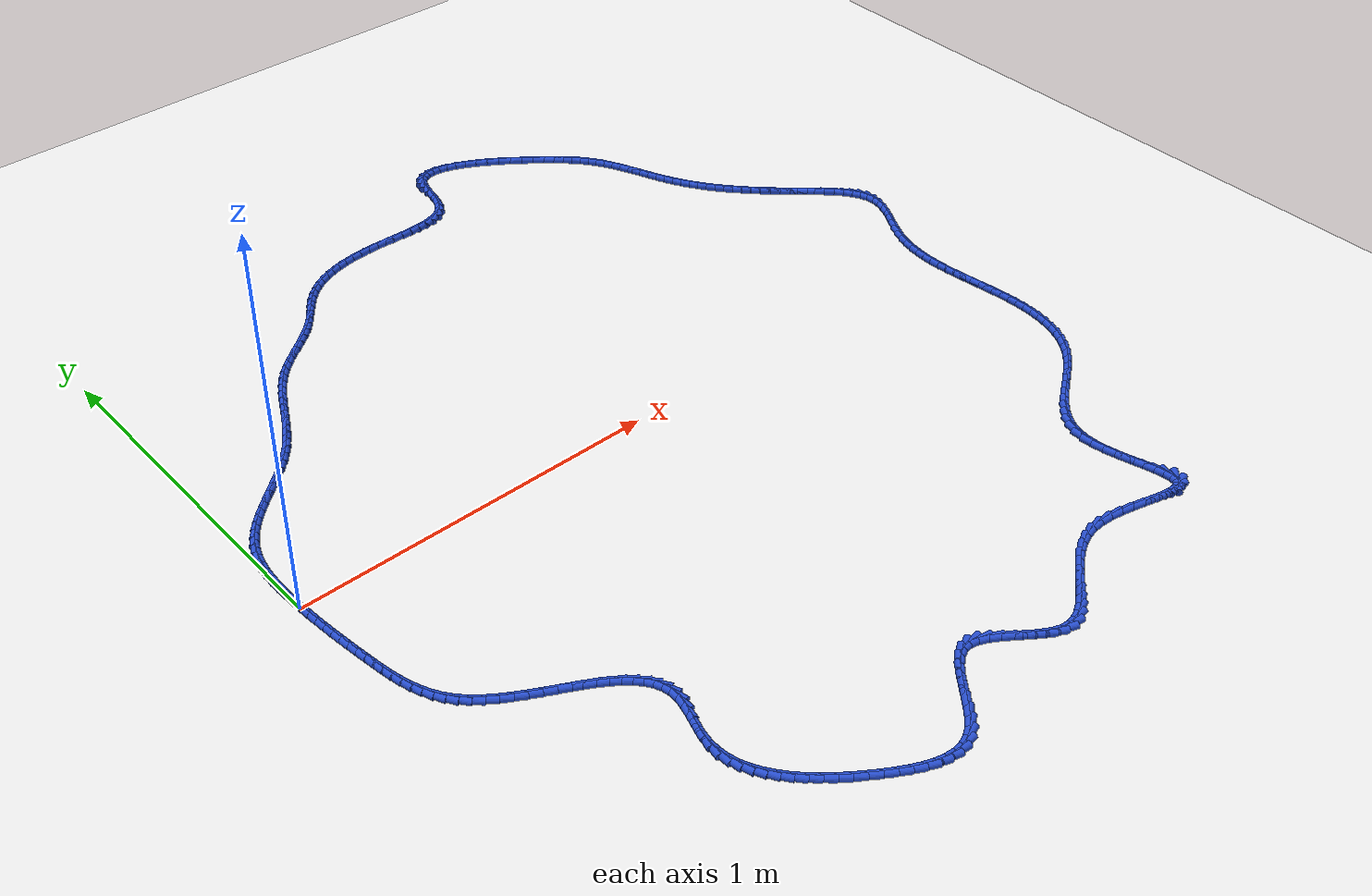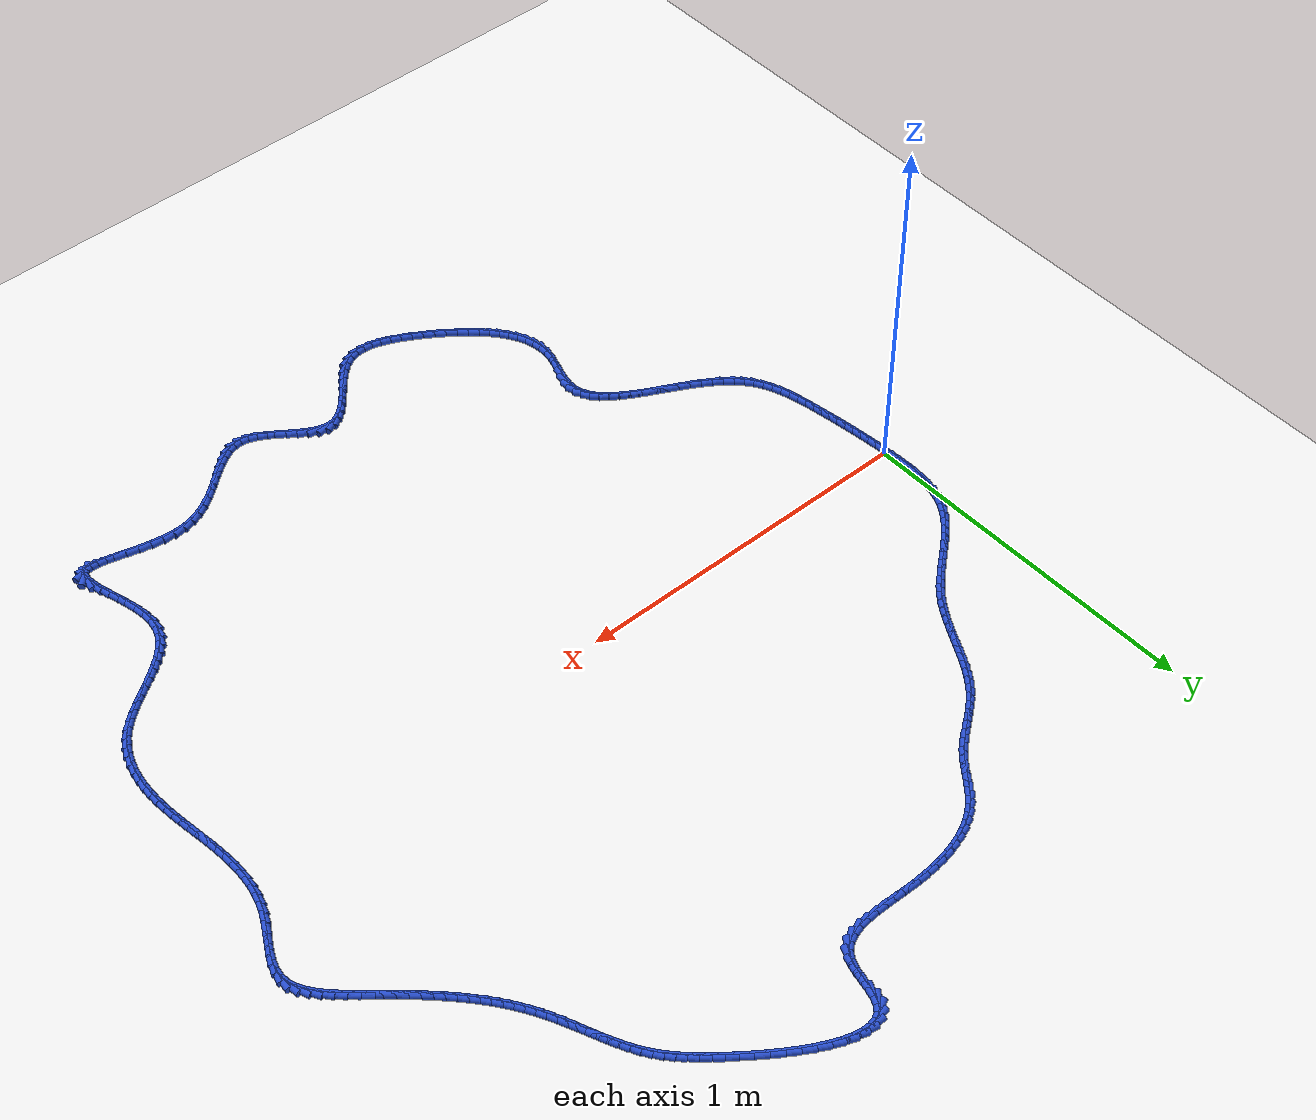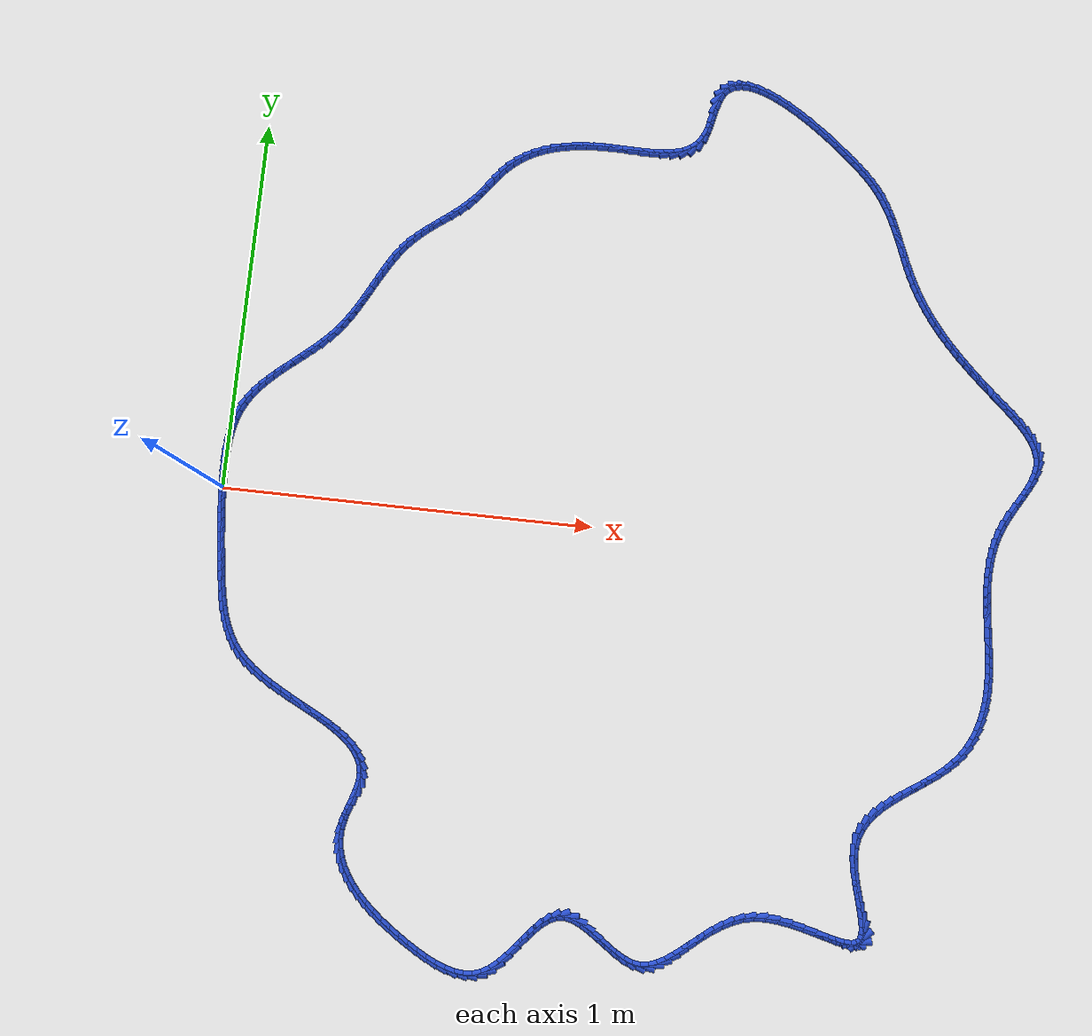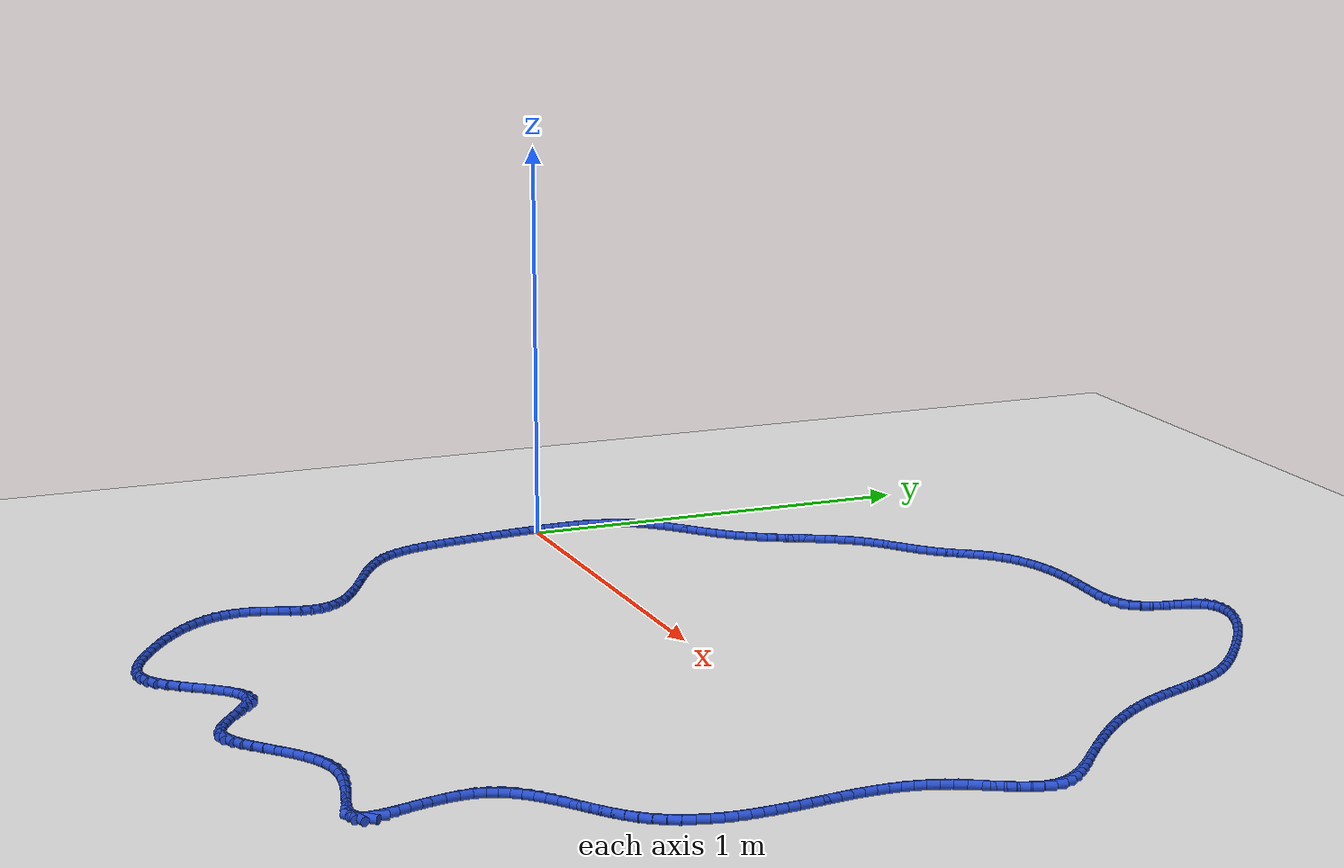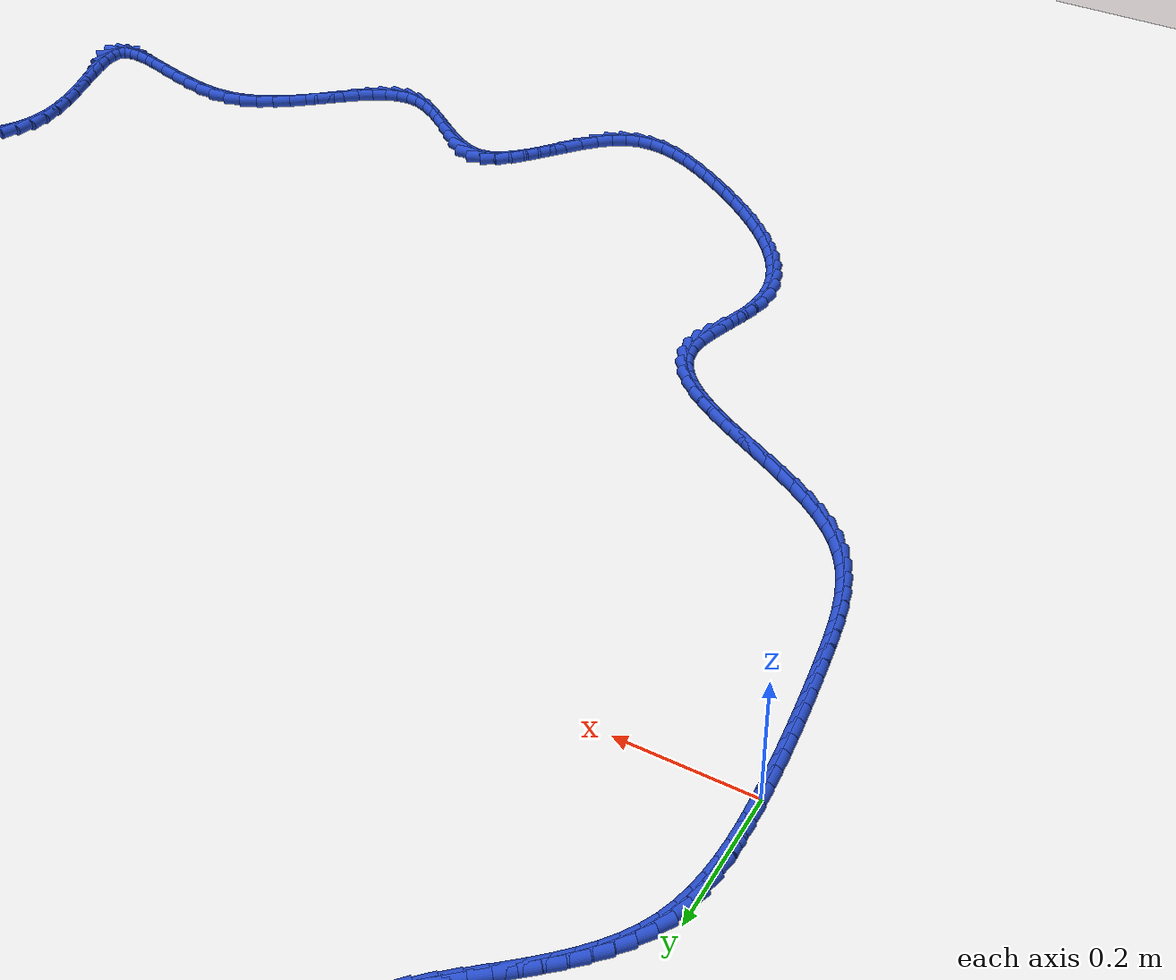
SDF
<sdf version="1.6">
 <world name="default">
  <light name="sun" type="directional">
   <pose>0 0 10 0 -0 0</pose>
   <diffuse>0.8 0.8 0.8 1</diffuse>
   <specular>0.2 0.2 0.2 1</specular>
   <attenuation>
    <range>1000</range>
    <constant>0.9</constant>
    <linear>0.01</linear>
    <quadratic>0.001</quadratic>
   </attenuation>
   <direction>-0.5 0.1 -0.9</direction>
  </light>
  <model name="ground_plane">
   <static>1</static>
   <link name="link">
    <collision name="collision">
     <geometry><plane><normal>0 0 1</normal><size>100 100</size></plane></geometry>
     <surface><friction><ode><mu>100</mu><mu2>50</mu2></ode></friction></surface>
    </collision>
    <visual name="visual">
     <cast_shadows>0</cast_shadows>
     <geometry><plane><normal>0 0 1</normal><size>100 100</size></plane></geometry>
     <material>
      <script><uri>file://media/materials/scripts/gazebo.material</uri><name>Gazebo/WhiteGlow</name></script>
     </material>
    </visual>
   </link>
  </model>
  <gravity>0 0 -9.8</gravity>
  <magnetic_field>6e-06 2.3e-05 -4.2e-05</magnetic_field>
  <atmosphere type="adiabatic"/>
  <physics name="default_physics" default="0" type="ode">
   <max_step_size>0.001</max_step_size>
   <real_time_factor>1</real_time_factor>
   <real_time_update_rate>1000</real_time_update_rate>
  </physics>
  <scene><ambient>0.4 0.4 0.4 1</ambient><background>0.7 0.7 0.7 1</background><shadows>1</shadows></scene>
  <spherical_coordinates>
   <surface_model>EARTH_WGS84</surface_model>
   <latitude_deg>0</latitude_deg>
   <longitude_deg>0</longitude_deg>
   <elevation>0</elevation>
   <heading_deg>0</heading_deg>
  </spherical_coordinates>
  <model name="line">
   <link name="link_0">
    <pose>-3.144186300207963e-18 -2.7755575615628914e-17 0.01 0 1.57 -1.5155655868217317</pose>
    <collision name="collision">
     <geometry><cylinder><radius>0.01</radius><length>0.08</length></cylinder></geometry>
    </collision>
    <visual name="visual">
     <material>
      <script><name>Gazebo/Blue</name><uri>file://media/materials/scripts/gazebo.material</uri></script>
     </material>
     <geometry><cylinder><radius>0.01</radius><length>0.08</length></cylinder></geometry>
    </visual>
   </link>
   <link name="link_1">
    <pose>-0.0015131828939657498 0.027369612644585345 0.01 0 1.57 -1.5385693356199552</pose>
    <collision name="collision">
     <geometry><cylinder><radius>0.01</radius><length>0.08</length></cylinder></geometry>
    </collision>
    <visual name="visual">
     <material>
      <script><name>Gazebo/Blue</name><uri>file://media/materials/scripts/gazebo.material</uri></script>
     </material>
     <geometry><cylinder><radius>0.01</radius><length>0.08</length></cylinder></geometry>
    </visual>
   </link>
   <link name="link_2">
    <pose>-0.0024024075205045657 0.05495260222829566 0.01 0 1.57 1.5706447185464925</pose>
    <collision name="collision">
     <geometry><cylinder><radius>0.01</radius><length>0.08</length></cylinder></geometry>
    </collision>
    <visual name="visual">
     <material>
      <script><name>Gazebo/Blue</name><uri>file://media/materials/scripts/gazebo.material</uri></script>
     </material>
     <geometry><cylinder><radius>0.01</radius><length>0.08</length></cylinder></geometry>
    </visual>
   </link>
   <link name="link_3">
    <pose>-0.0023982279416030626 0.08252088372666737 0.01 0 1.57 1.5281137982298083</pose>
    <collision name="collision">
     <geometry><cylinder><radius>0.01</radius><length>0.08</length></cylinder></geometry>
    </collision>
    <visual name="visual">
     <material>
      <script><name>Gazebo/Blue</name><uri>file://media/materials/scripts/gazebo.material</uri></script>
     </material>
     <geometry><cylinder><radius>0.01</radius><length>0.08</length></cylinder></geometry>
    </visual>
   </link>
   <link name="link_4">
    <pose>-0.0012311982192478557 0.10984637211523679 0.01 0 1.57 1.4743043803389275</pose>
    <collision name="collision">
     <geometry><cylinder><radius>0.01</radius><length>0.08</length></cylinder></geometry>
    </collision>
    <visual name="visual">
     <material>
      <script><name>Gazebo/Blue</name><uri>file://media/materials/scripts/gazebo.material</uri></script>
     </material>
     <geometry><cylinder><radius>0.01</radius><length>0.08</length></cylinder></geometry>
    </visual>
   </link>
   <link name="link_5">
    <pose>0.001368127584574442 0.13670098236954034 0.01 0 1.57 1.4078136785738362</pose>
    <collision name="collision">
     <geometry><cylinder><radius>0.01</radius><length>0.08</length></cylinder></geometry>
    </collision>
    <visual name="visual">
     <material>
      <script><name>Gazebo/Blue</name><uri>file://media/materials/scripts/gazebo.material</uri></script>
     </material>
     <geometry><cylinder><radius>0.01</radius><length>0.08</length></cylinder></geometry>
    </visual>
   </link>
   <link name="link_6">
    <pose>0.00566919540787722 0.1628566294651144 0.01 0 1.57 1.327119838038077</pose>
    <collision name="collision">
     <geometry><cylinder><radius>0.01</radius><length>0.08</length></cylinder></geometry>
    </collision>
    <visual name="visual">
     <material>
      <script><name>Gazebo/Blue</name><uri>file://media/materials/scripts/gazebo.material</uri></script>
     </material>
     <geometry><cylinder><radius>0.01</radius><length>0.08</length></cylinder></geometry>
    </visual>
   </link>
   <link name="link_7">
    <pose>0.01194145118867386 0.18808522837749536 0.01 0 1.57 1.230899075451566</pose>
    <collision name="collision">
     <geometry><cylinder><radius>0.01</radius><length>0.08</length></cylinder></geometry>
    </collision>
    <visual name="visual">
     <material>
      <script><name>Gazebo/Blue</name><uri>file://media/materials/scripts/gazebo.material</uri></script>
     </material>
     <geometry><cylinder><radius>0.01</radius><length>0.08</length></cylinder></geometry>
    </visual>
   </link>
   <link name="link_8">
    <pose>0.020454340864977754 0.2121586940822196 0.01 0 1.57 1.1193891497618498</pose>
    <collision name="collision">
     <geometry><cylinder><radius>0.01</radius><length>0.08</length></cylinder></geometry>
    </collision>
    <visual name="visual">
     <material>
      <script><name>Gazebo/Blue</name><uri>file://media/materials/scripts/gazebo.material</uri></script>
     </material>
     <geometry><cylinder><radius>0.01</radius><length>0.08</length></cylinder></geometry>
    </visual>
   </link>
   <link name="link_9">
    <pose>0.03146032617717873 0.23486119402031436 0.01 0 1.57 1.008697879521988</pose>
    <collision name="collision">
     <geometry><cylinder><radius>0.01</radius><length>0.08</length></cylinder></geometry>
    </collision>
    <visual name="visual">
     <material>
      <script><name>Gazebo/Blue</name><uri>file://media/materials/scripts/gazebo.material</uri></script>
     </material>
     <geometry><cylinder><radius>0.01</radius><length>0.08</length></cylinder></geometry>
    </visual>
   </link>
   <link name="link_10">
    <pose>0.044901599075144176 0.2562007254530614 0.01 0 1.57 0.9143473147754952</pose>
    <collision name="collision">
     <geometry><cylinder><radius>0.01</radius><length>0.08</length></cylinder></geometry>
    </collision>
    <visual name="visual">
     <material>
      <script><name>Gazebo/Blue</name><uri>file://media/materials/scripts/gazebo.material</uri></script>
     </material>
     <geometry><cylinder><radius>0.01</radius><length>0.08</length></cylinder></geometry>
    </visual>
   </link>
   <link name="link_11">
    <pose>0.06044908451519783 0.2763809786942422 0.01 0 1.57 0.8377700902250539</pose>
    <collision name="collision">
     <geometry><cylinder><radius>0.01</radius><length>0.08</length></cylinder></geometry>
    </collision>
    <visual name="visual">
     <material>
      <script><name>Gazebo/Blue</name><uri>file://media/materials/scripts/gazebo.material</uri></script>
     </material>
     <geometry><cylinder><radius>0.01</radius><length>0.08</length></cylinder></geometry>
    </visual>
   </link>
   <link name="link_12">
    <pose>0.07776456797215217 0.29561223731475306 0.01 0 1.57 0.7786116346671724</pose>
    <collision name="collision">
     <geometry><cylinder><radius>0.01</radius><length>0.08</length></cylinder></geometry>
    </collision>
    <visual name="visual">
     <material>
      <script><name>Gazebo/Blue</name><uri>file://media/materials/scripts/gazebo.material</uri></script>
     </material>
     <geometry><cylinder><radius>0.01</radius><length>0.08</length></cylinder></geometry>
    </visual>
   </link>
   <link name="link_13">
    <pose>0.0965098349208197 0.31410478488549026 0.01 0 1.57 0.7358971410100231</pose>
    <collision name="collision">
     <geometry><cylinder><radius>0.01</radius><length>0.08</length></cylinder></geometry>
    </collision>
    <visual name="visual">
     <material>
      <script><name>Gazebo/Blue</name><uri>file://media/materials/scripts/gazebo.material</uri></script>
     </material>
     <geometry><cylinder><radius>0.01</radius><length>0.08</length></cylinder></geometry>
    </visual>
   </link>
   <link name="link_14">
    <pose>0.11634667083601286 0.33206890497735025 0.01 0 1.57 0.7085490389407896</pose>
    <collision name="collision">
     <geometry><cylinder><radius>0.01</radius><length>0.08</length></cylinder></geometry>
    </collision>
    <visual name="visual">
     <material>
      <script><name>Gazebo/Blue</name><uri>file://media/materials/scripts/gazebo.material</uri></script>
     </material>
     <geometry><cylinder><radius>0.01</radius><length>0.08</length></cylinder></geometry>
    </visual>
   </link>
   <link name="link_15">
    <pose>0.13693686119254422 0.3497148811612294 0.01 0 1.57 0.6956836310359242</pose>
    <collision name="collision">
     <geometry><cylinder><radius>0.01</radius><length>0.08</length></cylinder></geometry>
    </collision>
    <visual name="visual">
     <material>
      <script><name>Gazebo/Blue</name><uri>file://media/materials/scripts/gazebo.material</uri></script>
     </material>
     <geometry><cylinder><radius>0.01</radius><length>0.08</length></cylinder></geometry>
    </visual>
   </link>
   <link name="link_16">
    <pose>0.15794219146522626 0.36725299700802405 0.01 0 1.57 0.6967502145703364</pose>
    <collision name="collision">
     <geometry><cylinder><radius>0.01</radius><length>0.08</length></cylinder></geometry>
    </collision>
    <visual name="visual">
     <material>
      <script><name>Gazebo/Blue</name><uri>file://media/materials/scripts/gazebo.material</uri></script>
     </material>
     <geometry><cylinder><radius>0.01</radius><length>0.08</length></cylinder></geometry>
    </visual>
   </link>
   <link name="link_17">
    <pose>0.1790244471288714 0.3848935360886303 0.01 0 1.57 0.7115730939831011</pose>
    <collision name="collision">
     <geometry><cylinder><radius>0.01</radius><length>0.08</length></cylinder></geometry>
    </collision>
    <visual name="visual">
     <material>
      <script><name>Gazebo/Blue</name><uri>file://media/materials/scripts/gazebo.material</uri></script>
     </material>
     <geometry><cylinder><radius>0.01</radius><length>0.08</length></cylinder></geometry>
    </visual>
   </link>
   <link name="link_18">
    <pose>0.19984541365829217 0.4028467819739448 0.01 0 1.57 0.7403297258838916</pose>
    <collision name="collision">
     <geometry><cylinder><radius>0.01</radius><length>0.08</length></cylinder></geometry>
    </collision>
    <visual name="visual">
     <material>
      <script><name>Gazebo/Blue</name><uri>file://media/materials/scripts/gazebo.material</uri></script>
     </material>
     <geometry><cylinder><radius>0.01</radius><length>0.08</length></cylinder></geometry>
    </visual>
   </link>
   <link name="link_19">
    <pose>0.220066876528301 0.4213230182348637 0.01 0 1.57 0.783469659659139</pose>
    <collision name="collision">
     <geometry><cylinder><radius>0.01</radius><length>0.08</length></cylinder></geometry>
    </collision>
    <visual name="visual">
     <material>
      <script><name>Gazebo/Blue</name><uri>file://media/materials/scripts/gazebo.material</uri></script>
     </material>
     <geometry><cylinder><radius>0.01</radius><length>0.08</length></cylinder></geometry>
    </visual>
   </link>
   <link name="link_20">
    <pose>0.23935062121371053 0.4405325284422835 0.01 0 1.57 0.8415551008620998</pose>
    <collision name="collision">
     <geometry><cylinder><radius>0.01</radius><length>0.08</length></cylinder></geometry>
    </collision>
    <visual name="visual">
     <material>
      <script><name>Gazebo/Blue</name><uri>file://media/materials/scripts/gazebo.material</uri></script>
     </material>
     <geometry><cylinder><radius>0.01</radius><length>0.08</length></cylinder></geometry>
    </visual>
   </link>
   <link name="link_21">
    <pose>0.2573584343836197 0.4606855953335093 0.01 0 1.57 0.9100082846713267</pose>
    <collision name="collision">
     <geometry><cylinder><radius>0.01</radius><length>0.08</length></cylinder></geometry>
    </collision>
    <visual name="visual">
     <material>
      <script><name>Gazebo/Blue</name><uri>file://media/materials/scripts/gazebo.material</uri></script>
     </material>
     <geometry><cylinder><radius>0.01</radius><length>0.08</length></cylinder></geometry>
    </visual>
   </link>
   <link name="link_22">
    <pose>0.27386207834928405 0.4819157405813134 0.01 0 1.57 0.969997503382248</pose>
    <collision name="collision">
     <geometry><cylinder><radius>0.01</radius><length>0.08</length></cylinder></geometry>
    </collision>
    <visual name="visual">
     <material>
      <script><name>Gazebo/Blue</name><uri>file://media/materials/scripts/gazebo.material</uri></script>
     </material>
     <geometry><cylinder><radius>0.01</radius><length>0.08</length></cylinder></geometry>
    </visual>
   </link>
   <link name="link_23">
    <pose>0.2890443412236979 0.5040695970758848 0.01 0 1.57 1.0168056320549819</pose>
    <collision name="collision">
     <geometry><cylinder><radius>0.01</radius><length>0.08</length></cylinder></geometry>
    </collision>
    <visual name="visual">
     <material>
      <script><name>Gazebo/Blue</name><uri>file://media/materials/scripts/gazebo.material</uri></script>
     </material>
     <geometry><cylinder><radius>0.01</radius><length>0.08</length></cylinder></geometry>
    </visual>
   </link>
   <link name="link_24">
    <pose>0.3031840164467783 0.5269267876772736 0.01 0 1.57 1.050402651763237</pose>
    <collision name="collision">
     <geometry><cylinder><radius>0.01</radius><length>0.08</length></cylinder></geometry>
    </collision>
    <visual name="visual">
     <material>
      <script><name>Gazebo/Blue</name><uri>file://media/materials/scripts/gazebo.material</uri></script>
     </material>
     <geometry><cylinder><radius>0.01</radius><length>0.08</length></cylinder></geometry>
    </visual>
   </link>
   <link name="link_25">
    <pose>0.31655989745844215 0.55026693524553 0.01 0 1.57 1.0709055941381729</pose>
    <collision name="collision">
     <geometry><cylinder><radius>0.01</radius><length>0.08</length></cylinder></geometry>
    </collision>
    <visual name="visual">
     <material>
      <script><name>Gazebo/Blue</name><uri>file://media/materials/scripts/gazebo.material</uri></script>
     </material>
     <geometry><cylinder><radius>0.01</radius><length>0.08</length></cylinder></geometry>
    </visual>
   </link>
   <link name="link_26">
    <pose>0.3294507776986065 0.5738696626407044 0.01 0 1.57 1.0784041709291683</pose>
    <collision name="collision">
     <geometry><cylinder><radius>0.01</radius><length>0.08</length></cylinder></geometry>
    </collision>
    <visual name="visual">
     <material>
      <script><name>Gazebo/Blue</name><uri>file://media/materials/scripts/gazebo.material</uri></script>
     </material>
     <geometry><cylinder><radius>0.01</radius><length>0.08</length></cylinder></geometry>
    </visual>
   </link>
   <link name="link_27">
    <pose>0.3421354506071885 0.5975145927228465 0.01 0 1.57 1.0728559851785364</pose>
    <collision name="collision">
     <geometry><cylinder><radius>0.01</radius><length>0.08</length></cylinder></geometry>
    </collision>
    <visual name="visual">
     <material>
      <script><name>Gazebo/Blue</name><uri>file://media/materials/scripts/gazebo.material</uri></script>
     </material>
     <geometry><cylinder><radius>0.01</radius><length>0.08</length></cylinder></geometry>
    </visual>
   </link>
   <link name="link_28">
    <pose>0.35489270962410485 0.6209813483520068 0.01 0 1.57 1.0540453341446754</pose>
    <collision name="collision">
     <geometry><cylinder><radius>0.01</radius><length>0.08</length></cylinder></geometry>
    </collision>
    <visual name="visual">
     <material>
      <script><name>Gazebo/Blue</name><uri>file://media/materials/scripts/gazebo.material</uri></script>
     </material>
     <geometry><cylinder><radius>0.01</radius><length>0.08</length></cylinder></geometry>
    </visual>
   </link>
   <link name="link_29">
    <pose>0.368001348189273 0.6440495523882355 0.01 0 1.57 1.0216046861269452</pose>
    <collision name="collision">
     <geometry><cylinder><radius>0.01</radius><length>0.08</length></cylinder></geometry>
    </collision>
    <visual name="visual">
     <material>
      <script><name>Gazebo/Blue</name><uri>file://media/materials/scripts/gazebo.material</uri></script>
     </material>
     <geometry><cylinder><radius>0.01</radius><length>0.08</length></cylinder></geometry>
    </visual>
   </link>
   <link name="link_30">
    <pose>0.38174015974260983 0.6664988276915829 0.01 0 1.57 0.9751084401328263</pose>
    <collision name="collision">
     <geometry><cylinder><radius>0.01</radius><length>0.08</length></cylinder></geometry>
    </collision>
    <visual name="visual">
     <material>
      <script><name>Gazebo/Blue</name><uri>file://media/materials/scripts/gazebo.material</uri></script>
     </material>
     <geometry><cylinder><radius>0.01</radius><length>0.08</length></cylinder></geometry>
    </visual>
   </link>
   <link name="link_31">
    <pose>0.39638793772403197 0.6881087971220984 0.01 0 1.57 0.9142567050235809</pose>
    <collision name="collision">
     <geometry><cylinder><radius>0.01</radius><length>0.08</length></cylinder></geometry>
    </collision>
    <visual name="visual">
     <material>
      <script><name>Gazebo/Blue</name><uri>file://media/materials/scripts/gazebo.material</uri></script>
     </material>
     <geometry><cylinder><radius>0.01</radius><length>0.08</length></cylinder></geometry>
    </visual>
   </link>
   <link name="link_32">
    <pose>0.412223475573457 0.7086590835398332 0.01 0 1.57 0.8391795045580464</pose>
    <collision name="collision">
     <geometry><cylinder><radius>0.01</radius><length>0.08</length></cylinder></geometry>
    </collision>
    <visual name="visual">
     <material>
      <script><name>Gazebo/Blue</name><uri>file://media/materials/scripts/gazebo.material</uri></script>
     </material>
     <geometry><cylinder><radius>0.01</radius><length>0.08</length></cylinder></geometry>
    </visual>
   </link>
   <link name="link_33">
    <pose>0.42952521194756565 0.7279296246226837 0.01 0 1.57 0.7596950481839011</pose>
    <collision name="collision">
     <geometry><cylinder><radius>0.01</radius><length>0.08</length></cylinder></geometry>
    </collision>
    <visual name="visual">
     <material>
      <script><name>Gazebo/Blue</name><uri>file://media/materials/scripts/gazebo.material</uri></script>
     </material>
     <geometry><cylinder><radius>0.01</radius><length>0.08</length></cylinder></geometry>
    </visual>
   </link>
   <link name="link_34">
    <pose>0.44839693710184775 0.7458553327712897 0.01 0 1.57 0.6999803119897922</pose>
    <collision name="collision">
     <geometry><cylinder><radius>0.01</radius><length>0.08</length></cylinder></geometry>
    </collision>
    <visual name="visual">
     <material>
      <script><name>Gazebo/Blue</name><uri>file://media/materials/scripts/gazebo.material</uri></script>
     </material>
     <geometry><cylinder><radius>0.01</radius><length>0.08</length></cylinder></geometry>
    </visual>
   </link>
   <link name="link_35">
    <pose>0.46848640694426885 0.7627757836760003 0.01 0 1.57 0.6633917569379105</pose>
    <collision name="collision">
     <geometry><cylinder><radius>0.01</radius><length>0.08</length></cylinder></geometry>
    </collision>
    <visual name="visual">
     <material>
      <script><name>Gazebo/Blue</name><uri>file://media/materials/scripts/gazebo.material</uri></script>
     </material>
     <geometry><cylinder><radius>0.01</radius><length>0.08</length></cylinder></geometry>
    </visual>
   </link>
   <link name="link_36">
    <pose>0.4893678729325579 0.7790957773963426 0.01 0 1.57 0.6491562956086534</pose>
    <collision name="collision">
     <geometry><cylinder><radius>0.01</radius><length>0.08</length></cylinder></geometry>
    </collision>
    <visual name="visual">
     <material>
      <script><name>Gazebo/Blue</name><uri>file://media/materials/scripts/gazebo.material</uri></script>
     </material>
     <geometry><cylinder><radius>0.01</radius><length>0.08</length></cylinder></geometry>
    </visual>
   </link>
   <link name="link_37">
    <pose>0.5106155865244453 0.7952201139918446 0.01 0 1.57 0.6567282749231638</pose>
    <collision name="collision">
     <geometry><cylinder><radius>0.01</radius><length>0.08</length></cylinder></geometry>
    </collision>
    <visual name="visual">
     <material>
      <script><name>Gazebo/Blue</name><uri>file://media/materials/scripts/gazebo.material</uri></script>
     </material>
     <geometry><cylinder><radius>0.01</radius><length>0.08</length></cylinder></geometry>
    </visual>
   </link>
   <link name="link_38">
    <pose>0.5318037991776596 0.8115535935220327 0.01 0 1.57 0.6859792857089673</pose>
    <collision name="collision">
     <geometry><cylinder><radius>0.01</radius><length>0.08</length></cylinder></geometry>
    </collision>
    <visual name="visual">
     <material>
      <script><name>Gazebo/Blue</name><uri>file://media/materials/scripts/gazebo.material</uri></script>
     </material>
     <geometry><cylinder><radius>0.01</radius><length>0.08</length></cylinder></geometry>
    </visual>
   </link>
   <link name="link_39">
    <pose>0.5525067623499312 0.8285010160464351 0.01 0 1.57 0.7370806622663758</pose>
    <collision name="collision">
     <geometry><cylinder><radius>0.01</radius><length>0.08</length></cylinder></geometry>
    </collision>
    <visual name="visual">
     <material>
      <script><name>Gazebo/Blue</name><uri>file://media/materials/scripts/gazebo.material</uri></script>
     </material>
     <geometry><cylinder><radius>0.01</radius><length>0.08</length></cylinder></geometry>
    </visual>
   </link>
   <link name="link_40">
    <pose>0.5722987274989889 0.8464671816245781 0.01 0 1.57 0.8092692131151384</pose>
    <collision name="collision">
     <geometry><cylinder><radius>0.01</radius><length>0.08</length></cylinder></geometry>
    </collision>
    <visual name="visual">
     <material>
      <script><name>Gazebo/Blue</name><uri>file://media/materials/scripts/gazebo.material</uri></script>
     </material>
     <geometry><cylinder><radius>0.01</radius><length>0.08</length></cylinder></geometry>
    </visual>
   </link>
   <link name="link_41">
    <pose>0.5907684205470087 0.8658403962260779 0.01 0 1.57 0.8761044099704459</pose>
    <collision name="collision">
     <geometry><cylinder><radius>0.01</radius><length>0.08</length></cylinder></geometry>
    </collision>
    <visual name="visual">
     <material>
      <script><name>Gazebo/Blue</name><uri>file://media/materials/scripts/gazebo.material</uri></script>
     </material>
     <geometry><cylinder><radius>0.01</radius><length>0.08</length></cylinder></geometry>
    </visual>
   </link>
   <link name="link_42">
    <pose>0.6079675867479735 0.8864813412912924 0.01 0 1.57 0.9072512508923722</pose>
    <collision name="collision">
     <geometry><cylinder><radius>0.01</radius><length>0.08</length></cylinder></geometry>
    </collision>
    <visual name="visual">
     <material>
      <script><name>Gazebo/Blue</name><uri>file://media/materials/scripts/gazebo.material</uri></script>
     </material>
     <geometry><cylinder><radius>0.01</radius><length>0.08</length></cylinder></geometry>
    </visual>
   </link>
   <link name="link_43">
    <pose>0.6244974074195689 0.9076245992522803 0.01 0 1.57 0.9013861456798573</pose>
    <collision name="collision">
     <geometry><cylinder><radius>0.01</radius><length>0.08</length></cylinder></geometry>
    </collision>
    <visual name="visual">
     <material>
      <script><name>Gazebo/Blue</name><uri>file://media/materials/scripts/gazebo.material</uri></script>
     </material>
     <geometry><cylinder><radius>0.01</radius><length>0.08</length></cylinder></geometry>
    </visual>
   </link>
   <link name="link_44">
    <pose>0.6409909805003186 0.9284683825865687 0.01 0 1.57 0.8572775292607597</pose>
    <collision name="collision">
     <geometry><cylinder><radius>0.01</radius><length>0.08</length></cylinder></geometry>
    </collision>
    <visual name="visual">
     <material>
      <script><name>Gazebo/Blue</name><uri>file://media/materials/scripts/gazebo.material</uri></script>
     </material>
     <geometry><cylinder><radius>0.01</radius><length>0.08</length></cylinder></geometry>
    </visual>
   </link>
   <link name="link_45">
    <pose>0.6580814039287448 0.9482109037716852 0.01 0 1.57 0.7728882888655754</pose>
    <collision name="collision">
     <geometry><cylinder><radius>0.01</radius><length>0.08</length></cylinder></geometry>
    </collision>
    <visual name="visual">
     <material>
      <script><name>Gazebo/Blue</name><uri>file://media/materials/scripts/gazebo.material</uri></script>
     </material>
     <geometry><cylinder><radius>0.01</radius><length>0.08</length></cylinder></geometry>
    </visual>
   </link>
   <link name="link_46">
    <pose>0.6763894388033018 0.9660665124020236 0.01 0 1.57 0.6671672778387407</pose>
    <collision name="collision">
     <geometry><cylinder><radius>0.01</radius><length>0.08</length></cylinder></geometry>
    </collision>
    <visual name="visual">
     <material>
      <script><name>Gazebo/Blue</name><uri>file://media/materials/scripts/gazebo.material</uri></script>
     </material>
     <geometry><cylinder><radius>0.01</radius><length>0.08</length></cylinder></geometry>
    </visual>
   </link>
   <link name="link_47">
    <pose>0.6962088199578458 0.9816773224768388 0.01 0 1.57 0.5645032360332911</pose>
    <collision name="collision">
     <geometry><cylinder><radius>0.01</radius><length>0.08</length></cylinder></geometry>
    </collision>
    <visual name="visual">
     <material>
      <script><name>Gazebo/Blue</name><uri>file://media/materials/scripts/gazebo.material</uri></script>
     </material>
     <geometry><cylinder><radius>0.01</radius><length>0.08</length></cylinder></geometry>
    </visual>
   </link>
   <link name="link_48">
    <pose>0.717480235989033 0.9951472476423672 0.01 0 1.57 0.4683213424950577</pose>
    <collision name="collision">
     <geometry><cylinder><radius>0.01</radius><length>0.08</length></cylinder></geometry>
    </collision>
    <visual name="visual">
     <material>
      <script><name>Gazebo/Blue</name><uri>file://media/materials/scripts/gazebo.material</uri></script>
     </material>
     <geometry><cylinder><radius>0.01</radius><length>0.08</length></cylinder></geometry>
    </visual>
   </link>
   <link name="link_49">
    <pose>0.7401268250953751 1.0066031582196746 0.01 0 1.57 0.38017533481034327</pose>
    <collision name="collision">
     <geometry><cylinder><radius>0.01</radius><length>0.08</length></cylinder></geometry>
    </collision>
    <visual name="visual">
     <material>
      <script><name>Gazebo/Blue</name><uri>file://media/materials/scripts/gazebo.material</uri></script>
     </material>
     <geometry><cylinder><radius>0.01</radius><length>0.08</length></cylinder></geometry>
    </visual>
   </link>
   <link name="link_50">
    <pose>0.7640717254753842 1.0161719245298282 0.01 0 1.57 0.3008566547140714</pose>
    <collision name="collision">
     <geometry><cylinder><radius>0.01</radius><length>0.08</length></cylinder></geometry>
    </collision>
    <visual name="visual">
     <material>
      <script><name>Gazebo/Blue</name><uri>file://media/materials/scripts/gazebo.material</uri></script>
     </material>
     <geometry><cylinder><radius>0.01</radius><length>0.08</length></cylinder></geometry>
    </visual>
   </link>
   <link name="link_51">
    <pose>0.7892380753275718 1.0239804168938933 0.01 0 1.57 0.23052446113596645</pose>
    <collision name="collision">
     <geometry><cylinder><radius>0.01</radius><length>0.08</length></cylinder></geometry>
    </collision>
    <visual name="visual">
     <material>
      <script><name>Gazebo/Blue</name><uri>file://media/materials/scripts/gazebo.material</uri></script>
     </material>
     <geometry><cylinder><radius>0.01</radius><length>0.08</length></cylinder></geometry>
    </visual>
   </link>
   <link name="link_52">
    <pose>0.8155490128504504 1.030155505632937 0.01 0 1.57 0.16889358243645897</pose>
    <collision name="collision">
     <geometry><cylinder><radius>0.01</radius><length>0.08</length></cylinder></geometry>
    </collision>
    <visual name="visual">
     <material>
      <script><name>Gazebo/Blue</name><uri>file://media/materials/scripts/gazebo.material</uri></script>
     </material>
     <geometry><cylinder><radius>0.01</radius><length>0.08</length></cylinder></geometry>
    </visual>
   </link>
   <link name="link_53">
    <pose>0.8429276762425315 1.0348240610680253 0.01 0 1.57 0.11541524773498889</pose>
    <collision name="collision">
     <geometry><cylinder><radius>0.01</radius><length>0.08</length></cylinder></geometry>
    </collision>
    <visual name="visual">
     <material>
      <script><name>Gazebo/Blue</name><uri>file://media/materials/scripts/gazebo.material</uri></script>
     </material>
     <geometry><cylinder><radius>0.01</radius><length>0.08</length></cylinder></geometry>
    </visual>
   </link>
   <link name="link_54">
    <pose>0.8712972037023271 1.0381129535202243 0.01 0 1.57 0.06941882080983323</pose>
    <collision name="collision">
     <geometry><cylinder><radius>0.01</radius><length>0.08</length></cylinder></geometry>
    </collision>
    <visual name="visual">
     <material>
      <script><name>Gazebo/Blue</name><uri>file://media/materials/scripts/gazebo.material</uri></script>
     </material>
     <geometry><cylinder><radius>0.01</radius><length>0.08</length></cylinder></geometry>
    </visual>
   </link>
   <link name="link_55">
    <pose>0.9005807334283493 1.0401490533106004 0.01 0 1.57 0.030208510134806306</pose>
    <collision name="collision">
     <geometry><cylinder><radius>0.01</radius><length>0.08</length></cylinder></geometry>
    </collision>
    <visual name="visual">
     <material>
      <script><name>Gazebo/Blue</name><uri>file://media/materials/scripts/gazebo.material</uri></script>
     </material>
     <geometry><cylinder><radius>0.01</radius><length>0.08</length></cylinder></geometry>
    </visual>
   </link>
   <link name="link_56">
    <pose>0.9307014036191092 1.0410592307602198 0.01 0 1.57 -0.0025927699023464827</pose>
    <collision name="collision">
     <geometry><cylinder><radius>0.01</radius><length>0.08</length></cylinder></geometry>
    </collision>
    <visual name="visual">
     <material>
      <script><name>Gazebo/Blue</name><uri>file://media/materials/scripts/gazebo.material</uri></script>
     </material>
     <geometry><cylinder><radius>0.01</radius><length>0.08</length></cylinder></geometry>
    </visual>
   </link>
   <link name="link_57">
    <pose>0.9615745627484784 1.0409791835830675 0.01 0 1.57 -0.021577090216991536</pose>
    <collision name="collision">
     <geometry><cylinder><radius>0.01</radius><length>0.08</length></cylinder></geometry>
    </collision>
    <visual name="visual">
     <material>
      <script><name>Gazebo/Blue</name><uri>file://media/materials/scripts/gazebo.material</uri></script>
     </material>
     <geometry><cylinder><radius>0.01</radius><length>0.08</length></cylinder></geometry>
    </visual>
   </link>
   <link name="link_58">
    <pose>0.9928871508688212 1.040303444172828 0.01 0 1.57 -0.01868479128936091</pose>
    <collision name="collision">
     <geometry><cylinder><radius>0.01</radius><length>0.08</length></cylinder></geometry>
    </collision>
    <visual name="visual">
     <material>
      <script><name>Gazebo/Blue</name><uri>file://media/materials/scripts/gazebo.material</uri></script>
     </material>
     <geometry><cylinder><radius>0.01</radius><length>0.08</length></cylinder></geometry>
    </visual>
   </link>
   <link name="link_59">
    <pose>1.024066444886732 1.039720797765194 0.01 0 1.57 0.007064394103406492</pose>
    <collision name="collision">
     <geometry><cylinder><radius>0.01</radius><length>0.08</length></cylinder></geometry>
    </collision>
    <visual name="visual">
     <material>
      <script><name>Gazebo/Blue</name><uri>file://media/materials/scripts/gazebo.material</uri></script>
     </material>
     <geometry><cylinder><radius>0.01</radius><length>0.08</length></cylinder></geometry>
    </visual>
   </link>
   <link name="link_60">
    <pose>1.0545256487911034 1.0399359771652195 0.01 0 1.57 0.05885481272148601</pose>
    <collision name="collision">
     <geometry><cylinder><radius>0.01</radius><length>0.08</length></cylinder></geometry>
    </collision>
    <visual name="visual">
     <material>
      <script><name>Gazebo/Blue</name><uri>file://media/materials/scripts/gazebo.material</uri></script>
     </material>
     <geometry><cylinder><radius>0.01</radius><length>0.08</length></cylinder></geometry>
    </visual>
   </link>
   <link name="link_61">
    <pose>1.08367796657083 1.0416537151779588 0.01 0 1.57 0.14300918004466553</pose>
    <collision name="collision">
     <geometry><cylinder><radius>0.01</radius><length>0.08</length></cylinder></geometry>
    </collision>
    <visual name="visual">
     <material>
      <script><name>Gazebo/Blue</name><uri>file://media/materials/scripts/gazebo.material</uri></script>
     </material>
     <geometry><cylinder><radius>0.01</radius><length>0.08</length></cylinder></geometry>
    </visual>
   </link>
   <link name="link_62">
    <pose>1.1109366022148055 1.045578744608467 0.01 0 1.57 0.26923124337227994</pose>
    <collision name="collision">
     <geometry><cylinder><radius>0.01</radius><length>0.08</length></cylinder></geometry>
    </collision>
    <visual name="visual">
     <material>
      <script><name>Gazebo/Blue</name><uri>file://media/materials/scripts/gazebo.material</uri></script>
     </material>
     <geometry><cylinder><radius>0.01</radius><length>0.08</length></cylinder></geometry>
    </visual>
   </link>
   <link name="link_63">
    <pose>1.1357147597119244 1.0524157982617992 0.01 0 1.57 0.44873913834401596</pose>
    <collision name="collision">
     <geometry><cylinder><radius>0.01</radius><length>0.08</length></cylinder></geometry>
    </collision>
    <visual name="visual">
     <material>
      <script><name>Gazebo/Blue</name><uri>file://media/materials/scripts/gazebo.material</uri></script>
     </material>
     <geometry><cylinder><radius>0.01</radius><length>0.08</length></cylinder></geometry>
    </visual>
   </link>
   <link name="link_64">
    <pose>1.1574256430510796 1.0628696089430094 0.01 0 1.57 0.6857807382556667</pose>
    <collision name="collision">
     <geometry><cylinder><radius>0.01</radius><length>0.08</length></cylinder></geometry>
    </collision>
    <visual name="visual">
     <material>
      <script><name>Gazebo/Blue</name><uri>file://media/materials/scripts/gazebo.material</uri></script>
     </material>
     <geometry><cylinder><radius>0.01</radius><length>0.08</length></cylinder></geometry>
    </visual>
   </link>
   <link name="link_65">
    <pose>1.175482456221166 1.0776449094571525 0.01 0 1.57 0.9612947553731795</pose>
    <collision name="collision">
     <geometry><cylinder><radius>0.01</radius><length>0.08</length></cylinder></geometry>
    </collision>
    <visual name="visual">
     <material>
      <script><name>Gazebo/Blue</name><uri>file://media/materials/scripts/gazebo.material</uri></script>
     </material>
     <geometry><cylinder><radius>0.01</radius><length>0.08</length></cylinder></geometry>
    </visual>
   </link>
   <link name="link_66">
    <pose>1.1893030818605963 1.0974402068774374 0.01 0 1.57 1.1950962762282933</pose>
    <collision name="collision">
     <geometry><cylinder><radius>0.01</radius><length>0.08</length></cylinder></geometry>
    </collision>
    <visual name="visual">
     <material>
      <script><name>Gazebo/Blue</name><uri>file://media/materials/scripts/gazebo.material</uri></script>
     </material>
     <geometry><cylinder><radius>0.01</radius><length>0.08</length></cylinder></geometry>
    </visual>
   </link>
   <link name="link_67">
    <pose>1.1990013495951997 1.122027933497424 0.01 0 1.57 1.3153344520101298</pose>
    <collision name="collision">
     <geometry><cylinder><radius>0.01</radius><length>0.08</length></cylinder></geometry>
    </collision>
    <visual name="visual">
     <material>
      <script><name>Gazebo/Blue</name><uri>file://media/materials/scripts/gazebo.material</uri></script>
     </material>
     <geometry><cylinder><radius>0.01</radius><length>0.08</length></cylinder></geometry>
    </visual>
   </link>
   <link name="link_68">
    <pose>1.2061188783692312 1.1492806072459916 0.01 0 1.57 1.3476424005962873</pose>
    <collision name="collision">
     <geometry><cylinder><radius>0.01</radius><length>0.08</length></cylinder></geometry>
    </collision>
    <visual name="visual">
     <material>
      <script><name>Gazebo/Blue</name><uri>file://media/materials/scripts/gazebo.material</uri></script>
     </material>
     <geometry><cylinder><radius>0.01</radius><length>0.08</length></cylinder></geometry>
    </visual>
   </link>
   <link name="link_69">
    <pose>1.2123724844480206 1.1768376164840482 0.01 0 1.57 1.299013703045849</pose>
    <collision name="collision">
     <geometry><cylinder><radius>0.01</radius><length>0.08</length></cylinder></geometry>
    </collision>
    <visual name="visual">
     <material>
      <script><name>Gazebo/Blue</name><uri>file://media/materials/scripts/gazebo.material</uri></script>
     </material>
     <geometry><cylinder><radius>0.01</radius><length>0.08</length></cylinder></geometry>
    </visual>
   </link>
   <link name="link_70">
    <pose>1.2194789840968956 1.2023383495725006 0.01 0 1.57 1.140623644467258</pose>
    <collision name="collision">
     <geometry><cylinder><radius>0.01</radius><length>0.08</length></cylinder></geometry>
    </collision>
    <visual name="visual">
     <material>
      <script><name>Gazebo/Blue</name><uri>file://media/materials/scripts/gazebo.material</uri></script>
     </material>
     <geometry><cylinder><radius>0.01</radius><length>0.08</length></cylinder></geometry>
    </visual>
   </link>
   <link name="link_71">
    <pose>1.2291537634521648 1.2234241077929882 0.01 0 1.57 0.8430474923591013</pose>
    <collision name="collision">
     <geometry><cylinder><radius>0.01</radius><length>0.08</length></cylinder></geometry>
    </collision>
    <visual name="visual">
     <material>
      <script><name>Gazebo/Blue</name><uri>file://media/materials/scripts/gazebo.material</uri></script>
     </material>
     <geometry><cylinder><radius>0.01</radius><length>0.08</length></cylinder></geometry>
    </visual>
   </link>
   <link name="link_72">
    <pose>1.2425609192650893 1.238473589457515 0.01 0 1.57 0.4998736898436517</pose>
    <collision name="collision">
     <geometry><cylinder><radius>0.01</radius><length>0.08</length></cylinder></geometry>
    </collision>
    <visual name="visual">
     <material>
      <script><name>Gazebo/Blue</name><uri>file://media/materials/scripts/gazebo.material</uri></script>
     </material>
     <geometry><cylinder><radius>0.01</radius><length>0.08</length></cylinder></geometry>
    </visual>
   </link>
   <link name="link_73">
    <pose>1.2594819613897101 1.2477148219235825 0.01 0 1.57 0.19478090766457262</pose>
    <collision name="collision">
     <geometry><cylinder><radius>0.01</radius><length>0.08</length></cylinder></geometry>
    </collision>
    <visual name="visual">
     <material>
      <script><name>Gazebo/Blue</name><uri>file://media/materials/scripts/gazebo.material</uri></script>
     </material>
     <geometry><cylinder><radius>0.01</radius><length>0.08</length></cylinder></geometry>
    </visual>
   </link>
   <link name="link_74">
    <pose>1.2794851355663666 1.2516610916673905 0.01 0 1.57 -0.03686080259224466</pose>
    <collision name="collision">
     <geometry><cylinder><radius>0.01</radius><length>0.08</length></cylinder></geometry>
    </collision>
    <visual name="visual">
     <material>
      <script><name>Gazebo/Blue</name><uri>file://media/materials/scripts/gazebo.material</uri></script>
     </material>
     <geometry><cylinder><radius>0.01</radius><length>0.08</length></cylinder></geometry>
    </visual>
   </link>
   <link name="link_75">
    <pose>1.302138687535398 1.250825685165139 0.01 0 1.57 -0.20239152097631471</pose>
    <collision name="collision">
     <geometry><cylinder><radius>0.01</radius><length>0.08</length></cylinder></geometry>
    </collision>
    <visual name="visual">
     <material>
      <script><name>Gazebo/Blue</name><uri>file://media/materials/scripts/gazebo.material</uri></script>
     </material>
     <geometry><cylinder><radius>0.01</radius><length>0.08</length></cylinder></geometry>
    </visual>
   </link>
   <link name="link_76">
    <pose>1.327010863037144 1.245721888893028 0.01 0 1.57 -0.3208236101117591</pose>
    <collision name="collision">
     <geometry><cylinder><radius>0.01</radius><length>0.08</length></cylinder></geometry>
    </collision>
    <visual name="visual">
     <material>
      <script><name>Gazebo/Blue</name><uri>file://media/materials/scripts/gazebo.material</uri></script>
     </material>
     <geometry><cylinder><radius>0.01</radius><length>0.08</length></cylinder></geometry>
    </visual>
   </link>
   <link name="link_77">
    <pose>1.3536699078119445 1.236862989327258 0.01 0 1.57 -0.4077426034506965</pose>
    <collision name="collision">
     <geometry><cylinder><radius>0.01</radius><length>0.08</length></cylinder></geometry>
    </collision>
    <visual name="visual">
     <material>
      <script><name>Gazebo/Blue</name><uri>file://media/materials/scripts/gazebo.material</uri></script>
     </material>
     <geometry><cylinder><radius>0.01</radius><length>0.08</length></cylinder></geometry>
    </visual>
   </link>
   <link name="link_78">
    <pose>1.3816840676001394 1.2247622729440288 0.01 0 1.57 -0.473563795478326</pose>
    <collision name="collision">
     <geometry><cylinder><radius>0.01</radius><length>0.08</length></cylinder></geometry>
    </collision>
    <visual name="visual">
     <material>
      <script><name>Gazebo/Blue</name><uri>file://media/materials/scripts/gazebo.material</uri></script>
     </material>
     <geometry><cylinder><radius>0.01</radius><length>0.08</length></cylinder></geometry>
    </visual>
   </link>
   <link name="link_79">
    <pose>1.4106215881420676 1.209933026219541 0.01 0 1.57 -0.5249630856622551</pose>
    <collision name="collision">
     <geometry><cylinder><radius>0.01</radius><length>0.08</length></cylinder></geometry>
    </collision>
    <visual name="visual">
     <material>
      <script><name>Gazebo/Blue</name><uri>file://media/materials/scripts/gazebo.material</uri></script>
     </material>
     <geometry><cylinder><radius>0.01</radius><length>0.08</length></cylinder></geometry>
    </visual>
   </link>
   <link name="link_80">
    <pose>1.4400507151780688 1.192888535629994 0.01 0 1.57 -0.5662640610322742</pose>
    <collision name="collision">
     <geometry><cylinder><radius>0.01</radius><length>0.08</length></cylinder></geometry>
    </collision>
    <visual name="visual">
     <material>
      <script><name>Gazebo/Blue</name><uri>file://media/materials/scripts/gazebo.material</uri></script>
     </material>
     <geometry><cylinder><radius>0.01</radius><length>0.08</length></cylinder></geometry>
    </visual>
   </link>
   <link name="link_81">
    <pose>1.4695396944484826 1.174142087651589 0.01 0 1.57 -0.6003521095952925</pose>
    <collision name="collision">
     <geometry><cylinder><radius>0.01</radius><length>0.08</length></cylinder></geometry>
    </collision>
    <visual name="visual">
     <material>
      <script><name>Gazebo/Blue</name><uri>file://media/materials/scripts/gazebo.material</uri></script>
     </material>
     <geometry><cylinder><radius>0.01</radius><length>0.08</length></cylinder></geometry>
    </visual>
   </link>
   <link name="link_82">
    <pose>1.4986567716936496 1.1542069687605245 0.01 0 1.57 -0.6292333115517629</pose>
    <collision name="collision">
     <geometry><cylinder><radius>0.01</radius><length>0.08</length></cylinder></geometry>
    </collision>
    <visual name="visual">
     <material>
      <script><name>Gazebo/Blue</name><uri>file://media/materials/scripts/gazebo.material</uri></script>
     </material>
     <geometry><cylinder><radius>0.01</radius><length>0.08</length></cylinder></geometry>
    </visual>
   </link>
   <link name="link_83">
    <pose>1.5269701926539083 1.1335964654330026 0.01 0 1.57 -0.6543802176660588</pose>
    <collision name="collision">
     <geometry><cylinder><radius>0.01</radius><length>0.08</length></cylinder></geometry>
    </collision>
    <visual name="visual">
     <material>
      <script><name>Gazebo/Blue</name><uri>file://media/materials/scripts/gazebo.material</uri></script>
     </material>
     <geometry><cylinder><radius>0.01</radius><length>0.08</length></cylinder></geometry>
    </visual>
   </link>
   <link name="link_84">
    <pose>1.5540482030695981 1.1128238641452224 0.01 0 1.57 -0.6769622745947211</pose>
    <collision name="collision">
     <geometry><cylinder><radius>0.01</radius><length>0.08</length></cylinder></geometry>
    </collision>
    <visual name="visual">
     <material>
      <script><name>Gazebo/Blue</name><uri>file://media/materials/scripts/gazebo.material</uri></script>
     </material>
     <geometry><cylinder><radius>0.01</radius><length>0.08</length></cylinder></geometry>
    </visual>
   </link>
   <link name="link_85">
    <pose>1.5794590486810591 1.0924024513733839 0.01 0 1.57 -0.6988539526534168</pose>
    <collision name="collision">
     <geometry><cylinder><radius>0.01</radius><length>0.08</length></cylinder></geometry>
    </collision>
    <visual name="visual">
     <material>
      <script><name>Gazebo/Blue</name><uri>file://media/materials/scripts/gazebo.material</uri></script>
     </material>
     <geometry><cylinder><radius>0.01</radius><length>0.08</length></cylinder></geometry>
    </visual>
   </link>
   <link name="link_86">
    <pose>1.6028214524818725 1.072770295519623 0.01 0 1.57 -0.7272483644969464</pose>
    <collision name="collision">
     <geometry><cylinder><radius>0.01</radius><length>0.08</length></cylinder></geometry>
    </collision>
    <visual name="visual">
     <material>
      <script><name>Gazebo/Blue</name><uri>file://media/materials/scripts/gazebo.material</uri></script>
     </material>
     <geometry><cylinder><radius>0.01</radius><length>0.08</length></cylinder></geometry>
    </visual>
   </link>
   <link name="link_87">
    <pose>1.6241285716240361 1.0538075064116323 0.01 0 1.57 -0.7657261601398747</pose>
    <collision name="collision">
     <geometry><cylinder><radius>0.01</radius><length>0.08</length></cylinder></geometry>
    </collision>
    <visual name="visual">
     <material>
      <script><name>Gazebo/Blue</name><uri>file://media/materials/scripts/gazebo.material</uri></script>
     </material>
     <geometry><cylinder><radius>0.01</radius><length>0.08</length></cylinder></geometry>
    </visual>
   </link>
   <link name="link_88">
    <pose>1.643541925592467 1.0351433107641346 0.01 0 1.57 -0.8143762361381833</pose>
    <collision name="collision">
     <geometry><cylinder><radius>0.01</radius><length>0.08</length></cylinder></geometry>
    </collision>
    <visual name="visual">
     <material>
      <script><name>Gazebo/Blue</name><uri>file://media/materials/scripts/gazebo.material</uri></script>
     </material>
     <geometry><cylinder><radius>0.01</radius><length>0.08</length></cylinder></geometry>
    </visual>
   </link>
   <link name="link_89">
    <pose>1.661223839671707 1.0164057345392028 0.01 0 1.57 -0.8721628618640554</pose>
    <collision name="collision">
     <geometry><cylinder><radius>0.01</radius><length>0.08</length></cylinder></geometry>
    </collision>
    <visual name="visual">
     <material>
      <script><name>Gazebo/Blue</name><uri>file://media/materials/scripts/gazebo.material</uri></script>
     </material>
     <geometry><cylinder><radius>0.01</radius><length>0.08</length></cylinder></geometry>
    </visual>
   </link>
   <link name="link_90">
    <pose>1.6773366391462947 0.9972228036989104 0.01 0 1.57 -0.9367756517731081</pose>
    <collision name="collision">
     <geometry><cylinder><radius>0.01</radius><length>0.08</length></cylinder></geometry>
    </collision>
    <visual name="visual">
     <material>
      <script><name>Gazebo/Blue</name><uri>file://media/materials/scripts/gazebo.material</uri></script>
     </material>
     <geometry><cylinder><radius>0.01</radius><length>0.08</length></cylinder></geometry>
    </visual>
   </link>
   <link name="link_91">
    <pose>1.6920426493007696 0.9772225442053298 0.01 0 1.57 -1.0046130788429728</pose>
    <collision name="collision">
     <geometry><cylinder><radius>0.01</radius><length>0.08</length></cylinder></geometry>
    </collision>
    <visual name="visual">
     <material>
      <script><name>Gazebo/Blue</name><uri>file://media/materials/scripts/gazebo.material</uri></script>
     </material>
     <geometry><cylinder><radius>0.01</radius><length>0.08</length></cylinder></geometry>
    </visual>
   </link>
   <link name="link_92">
    <pose>1.7055050954557922 0.95604174947842 0.01 0 1.57 -1.0657039013976144</pose>
    <collision name="collision">
     <geometry><cylinder><radius>0.01</radius><length>0.08</length></cylinder></geometry>
    </collision>
    <visual name="visual">
     <material>
      <script><name>Gazebo/Blue</name><uri>file://media/materials/scripts/gazebo.material</uri></script>
     </material>
     <geometry><cylinder><radius>0.01</radius><length>0.08</length></cylinder></geometry>
    </visual>
   </link>
   <link name="link_93">
    <pose>1.7179158651451343 0.9335964181170909 0.01 0 1.57 -1.1121636709397418</pose>
    <collision name="collision">
     <geometry><cylinder><radius>0.01</radius><length>0.08</length></cylinder></geometry>
    </collision>
    <visual name="visual">
     <material>
      <script><name>Gazebo/Blue</name><uri>file://media/materials/scripts/gazebo.material</uri></script>
     </material>
     <geometry><cylinder><radius>0.01</radius><length>0.08</length></cylinder></geometry>
    </visual>
   </link>
   <link name="link_94">
    <pose>1.7295007838472274 0.9101331460079343 0.01 0 1.57 -1.1448596393468295</pose>
    <collision name="collision">
     <geometry><cylinder><radius>0.01</radius><length>0.08</length></cylinder></geometry>
    </collision>
    <visual name="visual">
     <material>
      <script><name>Gazebo/Blue</name><uri>file://media/materials/scripts/gazebo.material</uri></script>
     </material>
     <geometry><cylinder><radius>0.01</radius><length>0.08</length></cylinder></geometry>
    </visual>
   </link>
   <link name="link_95">
    <pose>1.7404876416737591 0.8859176669797831 0.01 0 1.57 -1.1648777311139262</pose>
    <collision name="collision">
     <geometry><cylinder><radius>0.01</radius><length>0.08</length></cylinder></geometry>
    </collision>
    <visual name="visual">
     <material>
      <script><name>Gazebo/Blue</name><uri>file://media/materials/scripts/gazebo.material</uri></script>
     </material>
     <geometry><cylinder><radius>0.01</radius><length>0.08</length></cylinder></geometry>
    </visual>
   </link>
   <link name="link_96">
    <pose>1.7511042287364156 0.8612157148614714 0.01 0 1.57 -1.1729440643444753</pose>
    <collision name="collision">
     <geometry><cylinder><radius>0.01</radius><length>0.08</length></cylinder></geometry>
    </collision>
    <visual name="visual">
     <material>
      <script><name>Gazebo/Blue</name><uri>file://media/materials/scripts/gazebo.material</uri></script>
     </material>
     <geometry><cylinder><radius>0.01</radius><length>0.08</length></cylinder></geometry>
    </visual>
   </link>
   <link name="link_97">
    <pose>1.761578335146884 0.8362930234818324 0.01 0 1.57 -1.169388988273092</pose>
    <collision name="collision">
     <geometry><cylinder><radius>0.01</radius><length>0.08</length></cylinder></geometry>
    </collision>
    <visual name="visual">
     <material>
      <script><name>Gazebo/Blue</name><uri>file://media/materials/scripts/gazebo.material</uri></script>
     </material>
     <geometry><cylinder><radius>0.01</radius><length>0.08</length></cylinder></geometry>
    </visual>
   </link>
   <link name="link_98">
    <pose>1.7721377510168503 0.8114153266696994 0.01 0 1.57 -1.1541413308756854</pose>
    <collision name="collision">
     <geometry><cylinder><radius>0.01</radius><length>0.08</length></cylinder></geometry>
    </collision>
    <visual name="visual">
     <material>
      <script><name>Gazebo/Blue</name><uri>file://media/materials/scripts/gazebo.material</uri></script>
     </material>
     <geometry><cylinder><radius>0.01</radius><length>0.08</length></cylinder></geometry>
    </visual>
   </link>
   <link name="link_99">
    <pose>1.783010266458001 0.7868483582539054 0.01 0 1.57 -1.1267388934678915</pose>
    <collision name="collision">
     <geometry><cylinder><radius>0.01</radius><length>0.08</length></cylinder></geometry>
    </collision>
    <visual name="visual">
     <material>
      <script><name>Gazebo/Blue</name><uri>file://media/materials/scripts/gazebo.material</uri></script>
     </material>
     <geometry><cylinder><radius>0.01</radius><length>0.08</length></cylinder></geometry>
    </visual>
   </link>
   <link name="link_100">
    <pose>1.7944236715820232 0.762857852063284 0.01 0 1.57 -1.0883736327479534</pose>
    <collision name="collision">
     <geometry><cylinder><radius>0.01</radius><length>0.08</length></cylinder></geometry>
    </collision>
    <visual name="visual">
     <material>
      <script><name>Gazebo/Blue</name><uri>file://media/materials/scripts/gazebo.material</uri></script>
     </material>
     <geometry><cylinder><radius>0.01</radius><length>0.08</length></cylinder></geometry>
    </visual>
   </link>
   <link name="link_101">
    <pose>1.806572114352905 0.7396602573654656 0.01 0 1.57 -1.0478982110981125</pose>
    <collision name="collision">
     <geometry><cylinder><radius>0.01</radius><length>0.08</length></cylinder></geometry>
    </collision>
    <visual name="visual">
     <material>
      <script><name>Gazebo/Blue</name><uri>file://media/materials/scripts/gazebo.material</uri></script>
     </material>
     <geometry><cylinder><radius>0.01</radius><length>0.08</length></cylinder></geometry>
    </visual>
   </link>
   <link name="link_102">
    <pose>1.8194936155062438 0.7172433025386692 0.01 0 1.57 -1.008380726378558</pose>
    <collision name="collision">
     <geometry><cylinder><radius>0.01</radius><length>0.08</length></cylinder></geometry>
    </collision>
    <visual name="visual">
     <material>
      <script><name>Gazebo/Blue</name><uri>file://media/materials/scripts/gazebo.material</uri></script>
     </material>
     <geometry><cylinder><radius>0.01</radius><length>0.08</length></cylinder></geometry>
    </visual>
   </link>
   <link name="link_103">
    <pose>1.8331809378637245 0.6955284147116143 0.01 0 1.57 -0.9702636889963249</pose>
    <collision name="collision">
     <geometry><cylinder><radius>0.01</radius><length>0.08</length></cylinder></geometry>
    </collision>
    <visual name="visual">
     <material>
      <script><name>Gazebo/Blue</name><uri>file://media/materials/scripts/gazebo.material</uri></script>
     </material>
     <geometry><cylinder><radius>0.01</radius><length>0.08</length></cylinder></geometry>
    </visual>
   </link>
   <link name="link_104">
    <pose>1.8476268395067816 0.6744370140687218 0.01 0 1.57 -0.9339513973474087</pose>
    <collision name="collision">
     <geometry><cylinder><radius>0.01</radius><length>0.08</length></cylinder></geometry>
    </collision>
    <visual name="visual">
     <material>
      <script><name>Gazebo/Blue</name><uri>file://media/materials/scripts/gazebo.material</uri></script>
     </material>
     <geometry><cylinder><radius>0.01</radius><length>0.08</length></cylinder></geometry>
    </visual>
   </link>
   <link name="link_105">
    <pose>1.8628240785168488 0.6538905207944131 0.01 0 1.57 -0.8997954227482582</pose>
    <collision name="collision">
     <geometry><cylinder><radius>0.01</radius><length>0.08</length></cylinder></geometry>
    </collision>
    <visual name="visual">
     <material>
      <script><name>Gazebo/Blue</name><uri>file://media/materials/scripts/gazebo.material</uri></script>
     </material>
     <geometry><cylinder><radius>0.01</radius><length>0.08</length></cylinder></geometry>
    </visual>
   </link>
   <link name="link_106">
    <pose>1.8787654129753606 0.6338103550731089 0.01 0 1.57 -0.8680846432498506</pose>
    <collision name="collision">
     <geometry><cylinder><radius>0.01</radius><length>0.08</length></cylinder></geometry>
    </collision>
    <visual name="visual">
     <material>
      <script><name>Gazebo/Blue</name><uri>file://media/materials/scripts/gazebo.material</uri></script>
     </material>
     <geometry><cylinder><radius>0.01</radius><length>0.08</length></cylinder></geometry>
    </visual>
   </link>
   <link name="link_107">
    <pose>1.8954436009637514 0.6141179370892305 0.01 0 1.57 -0.8390404306166683</pose>
    <collision name="collision">
     <geometry><cylinder><radius>0.01</radius><length>0.08</length></cylinder></geometry>
    </collision>
    <visual name="visual">
     <material>
      <script><name>Gazebo/Blue</name><uri>file://media/materials/scripts/gazebo.material</uri></script>
     </material>
     <geometry><cylinder><radius>0.01</radius><length>0.08</length></cylinder></geometry>
    </visual>
   </link>
   <link name="link_108">
    <pose>1.9128514005634563 0.5947346870271988 0.01 0 1.57 -0.8128165860290484</pose>
    <collision name="collision">
     <geometry><cylinder><radius>0.01</radius><length>0.08</length></cylinder></geometry>
    </collision>
    <visual name="visual">
     <material>
      <script><name>Gazebo/Blue</name><uri>file://media/materials/scripts/gazebo.material</uri></script>
     </material>
     <geometry><cylinder><radius>0.01</radius><length>0.08</length></cylinder></geometry>
    </visual>
   </link>
   <link name="link_109">
    <pose>1.9309815698559094 0.5755820250714346 0.01 0 1.57 -0.7895031131428626</pose>
    <collision name="collision">
     <geometry><cylinder><radius>0.01</radius><length>0.08</length></cylinder></geometry>
    </collision>
    <visual name="visual">
     <material>
      <script><name>Gazebo/Blue</name><uri>file://media/materials/scripts/gazebo.material</uri></script>
     </material>
     <geometry><cylinder><radius>0.01</radius><length>0.08</length></cylinder></geometry>
    </visual>
   </link>
   <link name="link_110">
    <pose>1.9498268669225445 0.5565813714063595 0.01 0 1.57 -0.7691326776701348</pose>
    <collision name="collision">
     <geometry><cylinder><radius>0.01</radius><length>0.08</length></cylinder></geometry>
    </collision>
    <visual name="visual">
     <material>
      <script><name>Gazebo/Blue</name><uri>file://media/materials/scripts/gazebo.material</uri></script>
     </material>
     <geometry><cylinder><radius>0.01</radius><length>0.08</length></cylinder></geometry>
    </visual>
   </link>
   <link name="link_111">
    <pose>1.9693800498447969 0.5376541462163945 0.01 0 1.57 -0.7516886013548311</pose>
    <collision name="collision">
     <geometry><cylinder><radius>0.01</radius><length>0.08</length></cylinder></geometry>
    </collision>
    <visual name="visual">
     <material>
      <script><name>Gazebo/Blue</name><uri>file://media/materials/scripts/gazebo.material</uri></script>
     </material>
     <geometry><cylinder><radius>0.01</radius><length>0.08</length></cylinder></geometry>
    </visual>
   </link>
   <link name="link_112">
    <pose>1.9896338767041 0.5187217696859601 0.01 0 1.57 -0.7371134010757884</pose>
    <collision name="collision">
     <geometry><cylinder><radius>0.01</radius><length>0.08</length></cylinder></geometry>
    </collision>
    <visual name="visual">
     <material>
      <script><name>Gazebo/Blue</name><uri>file://media/materials/scripts/gazebo.material</uri></script>
     </material>
     <geometry><cylinder><radius>0.01</radius><length>0.08</length></cylinder></geometry>
    </visual>
   </link>
   <link name="link_113">
    <pose>2.0105811055818896 0.49970566199947763 0.01 0 1.57 -0.7253171274632365</pose>
    <collision name="collision">
     <geometry><cylinder><radius>0.01</radius><length>0.08</length></cylinder></geometry>
    </collision>
    <visual name="visual">
     <material>
      <script><name>Gazebo/Blue</name><uri>file://media/materials/scripts/gazebo.material</uri></script>
     </material>
     <geometry><cylinder><radius>0.01</radius><length>0.08</length></cylinder></geometry>
    </visual>
   </link>
   <link name="link_114">
    <pose>2.0322144945595997 0.48052724334136854 0.01 0 1.57 -0.7162503553660784</pose>
    <collision name="collision">
     <geometry><cylinder><radius>0.01</radius><length>0.08</length></cylinder></geometry>
    </collision>
    <visual name="visual">
     <material>
      <script><name>Gazebo/Blue</name><uri>file://media/materials/scripts/gazebo.material</uri></script>
     </material>
     <geometry><cylinder><radius>0.01</radius><length>0.08</length></cylinder></geometry>
    </visual>
   </link>
   <link name="link_115">
    <pose>2.0545236412146592 0.46110812252561945 0.01 0 1.57 -0.7154389428045672</pose>
    <collision name="collision">
     <geometry><cylinder><radius>0.01</radius><length>0.08</length></cylinder></geometry>
    </collision>
    <visual name="visual">
     <material>
      <script><name>Gazebo/Blue</name><uri>file://media/materials/scripts/gazebo.material</uri></script>
     </material>
     <geometry><cylinder><radius>0.01</radius><length>0.08</length></cylinder></geometry>
    </visual>
   </link>
   <link name="link_116">
    <pose>2.0772172680389756 0.4413866719410851 0.01 0 1.57 -0.7327088065797862</pose>
    <collision name="collision">
     <geometry><cylinder><radius>0.01</radius><length>0.08</length></cylinder></geometry>
    </collision>
    <visual name="visual">
     <material>
      <script><name>Gazebo/Blue</name><uri>file://media/materials/scripts/gazebo.material</uri></script>
     </material>
     <geometry><cylinder><radius>0.01</radius><length>0.08</length></cylinder></geometry>
    </visual>
   </link>
   <link name="link_117">
    <pose>2.0995061295883763 0.42133098438689554 0.01 0 1.57 -0.770326071234913</pose>
    <collision name="collision">
     <geometry><cylinder><radius>0.01</radius><length>0.08</length></cylinder></geometry>
    </collision>
    <visual name="visual">
     <material>
      <script><name>Gazebo/Blue</name><uri>file://media/materials/scripts/gazebo.material</uri></script>
     </material>
     <geometry><cylinder><radius>0.01</radius><length>0.08</length></cylinder></geometry>
    </visual>
   </link>
   <link name="link_118">
    <pose>2.120549886383691 0.40091220212696166 0.01 0 1.57 -0.8319440151642855</pose>
    <collision name="collision">
     <geometry><cylinder><radius>0.01</radius><length>0.08</length></cylinder></geometry>
    </collision>
    <visual name="visual">
     <material>
      <script><name>Gazebo/Blue</name><uri>file://media/materials/scripts/gazebo.material</uri></script>
     </material>
     <geometry><cylinder><radius>0.01</radius><length>0.08</length></cylinder></geometry>
    </visual>
   </link>
   <link name="link_119">
    <pose>2.1395081989457516 0.38010146742519385 0.01 0 1.57 -0.9240215232577753</pose>
    <collision name="collision">
     <geometry><cylinder><radius>0.01</radius><length>0.08</length></cylinder></geometry>
    </collision>
    <visual name="visual">
     <material>
      <script><name>Gazebo/Blue</name><uri>file://media/materials/scripts/gazebo.material</uri></script>
     </material>
     <geometry><cylinder><radius>0.01</radius><length>0.08</length></cylinder></geometry>
    </visual>
   </link>
   <link name="link_120">
    <pose>2.155540727795389 0.35886992254550254 0.01 0 1.57 -1.0559323850460622</pose>
    <collision name="collision">
     <geometry><cylinder><radius>0.01</radius><length>0.08</length></cylinder></geometry>
    </collision>
    <visual name="visual">
     <material>
      <script><name>Gazebo/Blue</name><uri>file://media/materials/scripts/gazebo.material</uri></script>
     </material>
     <geometry><cylinder><radius>0.01</radius><length>0.08</length></cylinder></geometry>
    </visual>
   </link>
   <link name="link_121">
    <pose>2.1678071334534352 0.3371887097517983 0.01 0 1.57 -1.2379847205708086</pose>
    <collision name="collision">
     <geometry><cylinder><radius>0.01</radius><length>0.08</length></cylinder></geometry>
    </collision>
    <visual name="visual">
     <material>
      <script><name>Gazebo/Blue</name><uri>file://media/materials/scripts/gazebo.material</uri></script>
     </material>
     <geometry><cylinder><radius>0.01</radius><length>0.08</length></cylinder></geometry>
    </visual>
   </link>
   <link name="link_122">
    <pose>2.1754670764407202 0.3150289713079912 0.01 0 1.57 -1.4730986204207743</pose>
    <collision name="collision">
     <geometry><cylinder><radius>0.01</radius><length>0.08</length></cylinder></geometry>
    </collision>
    <visual name="visual">
     <material>
      <script><name>Gazebo/Blue</name><uri>file://media/materials/scripts/gazebo.material</uri></script>
     </material>
     <geometry><cylinder><radius>0.01</radius><length>0.08</length></cylinder></geometry>
    </visual>
   </link>
   <link name="link_123">
    <pose>2.1776886475342283 0.29236212996247685 0.01 0 1.57 1.4272017197529758</pose>
    <collision name="collision">
     <geometry><cylinder><radius>0.01</radius><length>0.08</length></cylinder></geometry>
    </collision>
    <visual name="visual">
     <material>
      <script><name>Gazebo/Blue</name><uri>file://media/materials/scripts/gazebo.material</uri></script>
     </material>
     <geometry><cylinder><radius>0.01</radius><length>0.08</length></cylinder></geometry>
    </visual>
   </link>
   <link name="link_124">
    <pose>2.174337154576304 0.26918280569104563 0.01 0 1.57 1.2503567820717079</pose>
    <collision name="collision">
     <geometry><cylinder><radius>0.01</radius><length>0.08</length></cylinder></geometry>
    </collision>
    <visual name="visual">
     <material>
      <script><name>Gazebo/Blue</name><uri>file://media/materials/scripts/gazebo.material</uri></script>
     </material>
     <geometry><cylinder><radius>0.01</radius><length>0.08</length></cylinder></geometry>
    </visual>
   </link>
   <link name="link_125">
    <pose>2.1664859352680446 0.24552581103608961 0.01 0 1.57 1.1371549840233595</pose>
    <collision name="collision">
     <geometry><cylinder><radius>0.01</radius><length>0.08</length></cylinder></geometry>
    </collision>
    <visual name="visual">
     <material>
      <script><name>Gazebo/Blue</name><uri>file://media/materials/scripts/gazebo.material</uri></script>
     </material>
     <geometry><cylinder><radius>0.01</radius><length>0.08</length></cylinder></geometry>
    </visual>
   </link>
   <link name="link_126">
    <pose>2.15532869872585 0.22142996343780244 0.01 0 1.57 1.0743438635554179</pose>
    <collision name="collision">
     <geometry><cylinder><radius>0.01</radius><length>0.08</length></cylinder></geometry>
    </collision>
    <visual name="visual">
     <material>
      <script><name>Gazebo/Blue</name><uri>file://media/materials/scripts/gazebo.material</uri></script>
     </material>
     <geometry><cylinder><radius>0.01</radius><length>0.08</length></cylinder></geometry>
    </visual>
   </link>
   <link name="link_127">
    <pose>2.1420591540661227 0.19693408033637927 0.01 0 1.57 1.0521329771019805</pose>
    <collision name="collision">
     <geometry><cylinder><radius>0.01</radius><length>0.08</length></cylinder></geometry>
    </collision>
    <visual name="visual">
     <material>
      <script><name>Gazebo/Blue</name><uri>file://media/materials/scripts/gazebo.material</uri></script>
     </material>
     <geometry><cylinder><radius>0.01</radius><length>0.08</length></cylinder></geometry>
    </visual>
   </link>
   <link name="link_128">
    <pose>2.127871010405264 0.1720769791720139 0.01 0 1.57 1.0659944131884131</pose>
    <collision name="collision">
     <geometry><cylinder><radius>0.01</radius><length>0.08</length></cylinder></geometry>
    </collision>
    <visual name="visual">
     <material>
      <script><name>Gazebo/Blue</name><uri>file://media/materials/scripts/gazebo.material</uri></script>
     </material>
     <geometry><cylinder><radius>0.01</radius><length>0.08</length></cylinder></geometry>
    </visual>
   </link>
   <link name="link_129">
    <pose>2.1139579768596755 0.14689747738490055 0.01 0 1.57 1.1162166853875142</pose>
    <collision name="collision">
     <geometry><cylinder><radius>0.01</radius><length>0.08</length></cylinder></geometry>
    </collision>
    <visual name="visual">
     <material>
      <script><name>Gazebo/Blue</name><uri>file://media/materials/scripts/gazebo.material</uri></script>
     </material>
     <geometry><cylinder><radius>0.01</radius><length>0.08</length></cylinder></geometry>
    </visual>
   </link>
   <link name="link_130">
    <pose>2.101513762545758 0.12143439241523349 0.01 0 1.57 1.1998204948886244</pose>
    <collision name="collision">
     <geometry><cylinder><radius>0.01</radius><length>0.08</length></cylinder></geometry>
    </collision>
    <visual name="visual">
     <material>
      <script><name>Gazebo/Blue</name><uri>file://media/materials/scripts/gazebo.material</uri></script>
     </material>
     <geometry><cylinder><radius>0.01</radius><length>0.08</length></cylinder></geometry>
    </visual>
   </link>
   <link name="link_131">
    <pose>2.091512842899417 0.09572417671635959 0.01 0 1.57 1.2877654886029755</pose>
    <collision name="collision">
     <geometry><cylinder><radius>0.01</radius><length>0.08</length></cylinder></geometry>
    </collision>
    <visual name="visual">
     <material>
      <script><name>Gazebo/Blue</name><uri>file://media/materials/scripts/gazebo.material</uri></script>
     </material>
     <geometry><cylinder><radius>0.01</radius><length>0.08</length></cylinder></geometry>
    </visual>
   </link>
   <link name="link_132">
    <pose>2.0839710374079172 0.06979294122519494 0.01 0 1.57 1.3696117897772495</pose>
    <collision name="collision">
     <geometry><cylinder><radius>0.01</radius><length>0.08</length></cylinder></geometry>
    </collision>
    <visual name="visual">
     <material>
      <script><name>Gazebo/Blue</name><uri>file://media/materials/scripts/gazebo.material</uri></script>
     </material>
     <geometry><cylinder><radius>0.01</radius><length>0.08</length></cylinder></geometry>
    </visual>
   </link>
   <link name="link_133">
    <pose>2.078642202621174 0.04366397094926339 0.01 0 1.57 1.443669029669192</pose>
    <collision name="collision">
     <geometry><cylinder><radius>0.01</radius><length>0.08</length></cylinder></geometry>
    </collision>
    <visual name="visual">
     <material>
      <script><name>Gazebo/Blue</name><uri>file://media/materials/scripts/gazebo.material</uri></script>
     </material>
     <geometry><cylinder><radius>0.01</radius><length>0.08</length></cylinder></geometry>
    </visual>
   </link>
   <link name="link_134">
    <pose>2.0752801888118815 0.01736055082837355 0.01 0 1.57 1.5088319705163185</pose>
    <collision name="collision">
     <geometry><cylinder><radius>0.01</radius><length>0.08</length></cylinder></geometry>
    </collision>
    <visual name="visual">
     <material>
      <script><name>Gazebo/Blue</name><uri>file://media/materials/scripts/gazebo.material</uri></script>
     </material>
     <geometry><cylinder><radius>0.01</radius><length>0.08</length></cylinder></geometry>
    </visual>
   </link>
   <link name="link_135">
    <pose>2.073638846252731 -0.009094034197666388 0.01 0 1.57 1.5645208047001813</pose>
    <collision name="collision">
     <geometry><cylinder><radius>0.01</radius><length>0.08</length></cylinder></geometry>
    </collision>
    <visual name="visual">
     <material>
      <script><name>Gazebo/Blue</name><uri>file://media/materials/scripts/gazebo.material</uri></script>
     </material>
     <geometry><cylinder><radius>0.01</radius><length>0.08</length></cylinder></geometry>
    </visual>
   </link>
   <link name="link_136">
    <pose>2.0734720252164145 -0.035676499189047015 0.01 0 1.57 -1.5310395531557892</pose>
    <collision name="collision">
     <geometry><cylinder><radius>0.01</radius><length>0.08</length></cylinder></geometry>
    </collision>
    <visual name="visual">
     <material>
      <script><name>Gazebo/Blue</name><uri>file://media/materials/scripts/gazebo.material</uri></script>
     </material>
     <geometry><cylinder><radius>0.01</radius><length>0.08</length></cylinder></geometry>
    </visual>
   </link>
   <link name="link_137">
    <pose>2.0745335759756256 -0.06236355920596012 0.01 0 1.57 -1.4945938777242755</pose>
    <collision name="collision">
     <geometry><cylinder><radius>0.01</radius><length>0.08</length></cylinder></geometry>
    </collision>
    <visual name="visual">
     <material>
      <script><name>Gazebo/Blue</name><uri>file://media/materials/scripts/gazebo.material</uri></script>
     </material>
     <geometry><cylinder><radius>0.01</radius><length>0.08</length></cylinder></geometry>
    </visual>
   </link>
   <link name="link_138">
    <pose>2.0765773488030557 -0.08913192930859712 0.01 0 1.57 -1.4675413451723505</pose>
    <collision name="collision">
     <geometry><cylinder><radius>0.01</radius><length>0.08</length></cylinder></geometry>
    </collision>
    <visual name="visual">
     <material>
      <script><name>Gazebo/Blue</name><uri>file://media/materials/scripts/gazebo.material</uri></script>
     </material>
     <geometry><cylinder><radius>0.01</radius><length>0.08</length></cylinder></geometry>
    </visual>
   </link>
   <link name="link_139">
    <pose>2.079357193971397 -0.1159583245571494 0.01 0 1.57 -1.4496637124600082</pose>
    <collision name="collision">
     <geometry><cylinder><radius>0.01</radius><length>0.08</length></cylinder></geometry>
    </collision>
    <visual name="visual">
     <material>
      <script><name>Gazebo/Blue</name><uri>file://media/materials/scripts/gazebo.material</uri></script>
     </material>
     <geometry><cylinder><radius>0.01</radius><length>0.08</length></cylinder></geometry>
    </visual>
   </link>
   <link name="link_140">
    <pose>2.082626961753343 -0.14281946001180876 0.01 0 1.57 -1.4407857080998465</pose>
    <collision name="collision">
     <geometry><cylinder><radius>0.01</radius><length>0.08</length></cylinder></geometry>
    </collision>
    <visual name="visual">
     <material>
      <script><name>Gazebo/Blue</name><uri>file://media/materials/scripts/gazebo.material</uri></script>
     </material>
     <geometry><cylinder><radius>0.01</radius><length>0.08</length></cylinder></geometry>
    </visual>
   </link>
   <link name="link_141">
    <pose>2.0861405024215856 -0.1696920507327658 0.01 0 1.57 -1.4408160938373828</pose>
    <collision name="collision">
     <geometry><cylinder><radius>0.01</radius><length>0.08</length></cylinder></geometry>
    </collision>
    <visual name="visual">
     <material>
      <script><name>Gazebo/Blue</name><uri>file://media/materials/scripts/gazebo.material</uri></script>
     </material>
     <geometry><cylinder><radius>0.01</radius><length>0.08</length></cylinder></geometry>
    </visual>
   </link>
   <link name="link_142">
    <pose>2.0896516662488165 -0.1965528117802123 0.01 0 1.57 -1.4497669529349773</pose>
    <collision name="collision">
     <geometry><cylinder><radius>0.01</radius><length>0.08</length></cylinder></geometry>
    </collision>
    <visual name="visual">
     <material>
      <script><name>Gazebo/Blue</name><uri>file://media/materials/scripts/gazebo.material</uri></script>
     </material>
     <geometry><cylinder><radius>0.01</radius><length>0.08</length></cylinder></geometry>
    </visual>
   </link>
   <link name="link_143">
    <pose>2.092914303507729 -0.22337845821433977 0.01 0 1.57 -1.4677540689173079</pose>
    <collision name="collision">
     <geometry><cylinder><radius>0.01</radius><length>0.08</length></cylinder></geometry>
    </collision>
    <visual name="visual">
     <material>
      <script><name>Gazebo/Blue</name><uri>file://media/materials/scripts/gazebo.material</uri></script>
     </material>
     <geometry><cylinder><radius>0.01</radius><length>0.08</length></cylinder></geometry>
    </visual>
   </link>
   <link name="link_144">
    <pose>2.095682264471015 -0.2501457050953394 0.01 0 1.57 -1.4949782057749854</pose>
    <collision name="collision">
     <geometry><cylinder><radius>0.01</radius><length>0.08</length></cylinder></geometry>
    </collision>
    <visual name="visual">
     <material>
      <script><name>Gazebo/Blue</name><uri>file://media/materials/scripts/gazebo.material</uri></script>
     </material>
     <geometry><cylinder><radius>0.01</radius><length>0.08</length></cylinder></geometry>
    </visual>
   </link>
   <link name="link_145">
    <pose>2.097709399411366 -0.27683126748340275 0.01 0 1.57 -1.531684003943477</pose>
    <collision name="collision">
     <geometry><cylinder><radius>0.01</radius><length>0.08</length></cylinder></geometry>
    </collision>
    <visual name="visual">
     <material>
      <script><name>Gazebo/Blue</name><uri>file://media/materials/scripts/gazebo.material</uri></script>
     </material>
     <geometry><cylinder><radius>0.01</radius><length>0.08</length></cylinder></geometry>
    </visual>
   </link>
   <link name="link_146">
    <pose>2.098749558601476 -0.30341186043872204 0.01 0 1.57 1.5635015893545938</pose>
    <collision name="collision">
     <geometry><cylinder><radius>0.01</radius><length>0.08</length></cylinder></geometry>
    </collision>
    <visual name="visual">
     <material>
      <script><name>Gazebo/Blue</name><uri>file://media/materials/scripts/gazebo.material</uri></script>
     </material>
     <geometry><cylinder><radius>0.01</radius><length>0.08</length></cylinder></geometry>
    </visual>
   </link>
   <link name="link_147">
    <pose>2.0985565923140364 -0.329864199021487 0.01 0 1.57 1.507300403059409</pose>
    <collision name="collision">
     <geometry><cylinder><radius>0.01</radius><length>0.08</length></cylinder></geometry>
    </collision>
    <visual name="visual">
     <material>
      <script><name>Gazebo/Blue</name><uri>file://media/materials/scripts/gazebo.material</uri></script>
     </material>
     <geometry><cylinder><radius>0.01</radius><length>0.08</length></cylinder></geometry>
    </visual>
   </link>
   <link name="link_148">
    <pose>2.0968843508217394 -0.35616499829188975 0.01 0 1.57 1.4414727798368918</pose>
    <collision name="collision">
     <geometry><cylinder><radius>0.01</radius><length>0.08</length></cylinder></geometry>
    </collision>
    <visual name="visual">
     <material>
      <script><name>Gazebo/Blue</name><uri>file://media/materials/scripts/gazebo.material</uri></script>
     </material>
     <geometry><cylinder><radius>0.01</radius><length>0.08</length></cylinder></geometry>
    </visual>
   </link>
   <link name="link_149">
    <pose>2.093486684397278 -0.3822909733101218 0.01 0 1.57 1.3666255447218387</pose>
    <collision name="collision">
     <geometry><cylinder><radius>0.01</radius><length>0.08</length></cylinder></geometry>
    </collision>
    <visual name="visual">
     <material>
      <script><name>Gazebo/Blue</name><uri>file://media/materials/scripts/gazebo.material</uri></script>
     </material>
     <geometry><cylinder><radius>0.01</radius><length>0.08</length></cylinder></geometry>
    </visual>
   </link>
   <link name="link_150">
    <pose>2.0881196257879533 -0.4082117927885201 0.01 0 1.57 1.2838967339224017</pose>
    <collision name="collision">
     <geometry><cylinder><radius>0.01</radius><length>0.08</length></cylinder></geometry>
    </collision>
    <visual name="visual">
     <material>
      <script><name>Gazebo/Blue</name><uri>file://media/materials/scripts/gazebo.material</uri></script>
     </material>
     <geometry><cylinder><radius>0.01</radius><length>0.08</length></cylinder></geometry>
    </visual>
   </link>
   <link name="link_151">
    <pose>2.0805862826034613 -0.43374513931588143 0.01 0 1.57 1.1929212636502478</pose>
    <collision name="collision">
     <geometry><cylinder><radius>0.01</radius><length>0.08</length></cylinder></geometry>
    </collision>
    <visual name="visual">
     <material>
      <script><name>Gazebo/Blue</name><uri>file://media/materials/scripts/gazebo.material</uri></script>
     </material>
     <geometry><cylinder><radius>0.01</radius><length>0.08</length></cylinder></geometry>
    </visual>
   </link>
   <link name="link_152">
    <pose>2.0707351655181547 -0.45856210693154487 0.01 0 1.57 1.0925908687111168</pose>
    <collision name="collision">
     <geometry><cylinder><radius>0.01</radius><length>0.08</length></cylinder></geometry>
    </collision>
    <visual name="visual">
     <material>
      <script><name>Gazebo/Blue</name><uri>file://media/materials/scripts/gazebo.material</uri></script>
     </material>
     <geometry><cylinder><radius>0.01</radius><length>0.08</length></cylinder></geometry>
    </visual>
   </link>
   <link name="link_153">
    <pose>2.0584166331843936 -0.4823278232843032 0.01 0 1.57 0.9823032446369511</pose>
    <collision name="collision">
     <geometry><cylinder><radius>0.01</radius><length>0.08</length></cylinder></geometry>
    </collision>
    <visual name="visual">
     <material>
      <script><name>Gazebo/Blue</name><uri>file://media/materials/scripts/gazebo.material</uri></script>
     </material>
     <geometry><cylinder><radius>0.01</radius><length>0.08</length></cylinder></geometry>
    </visual>
   </link>
   <link name="link_154">
    <pose>2.0434810442545412 -0.5047074160229496 0.01 0 1.57 0.8655611623064244</pose>
    <collision name="collision">
     <geometry><cylinder><radius>0.01</radius><length>0.08</length></cylinder></geometry>
    </collision>
    <visual name="visual">
     <material>
      <script><name>Gazebo/Blue</name><uri>file://media/materials/scripts/gazebo.material</uri></script>
     </material>
     <geometry><cylinder><radius>0.01</radius><length>0.08</length></cylinder></geometry>
    </visual>
   </link>
   <link name="link_155">
    <pose>2.0258436305837217 -0.525426179032048 0.01 0 1.57 0.7657281394973803</pose>
    <collision name="collision">
     <geometry><cylinder><radius>0.01</radius><length>0.08</length></cylinder></geometry>
    </collision>
    <visual name="visual">
     <material>
      <script><name>Gazebo/Blue</name><uri>file://media/materials/scripts/gazebo.material</uri></script>
     </material>
     <geometry><cylinder><radius>0.01</radius><length>0.08</length></cylinder></geometry>
    </visual>
   </link>
   <link name="link_156">
    <pose>2.005871059837162 -0.544628087442473 0.01 0 1.57 0.6915455375175421</pose>
    <collision name="collision">
     <geometry><cylinder><radius>0.01</radius><length>0.08</length></cylinder></geometry>
    </collision>
    <visual name="visual">
     <material>
      <script><name>Gazebo/Blue</name><uri>file://media/materials/scripts/gazebo.material</uri></script>
     </material>
     <geometry><cylinder><radius>0.01</radius><length>0.08</length></cylinder></geometry>
    </visual>
   </link>
   <link name="link_157">
    <pose>1.9841218685797717 -0.5626350639653599 0.01 0 1.57 0.6409796865034896</pose>
    <collision name="collision">
     <geometry><cylinder><radius>0.01</radius><length>0.08</length></cylinder></geometry>
    </collision>
    <visual name="visual">
     <material>
      <script><name>Gazebo/Blue</name><uri>file://media/materials/scripts/gazebo.material</uri></script>
     </material>
     <geometry><cylinder><radius>0.01</radius><length>0.08</length></cylinder></geometry>
    </visual>
   </link>
   <link name="link_158">
    <pose>1.961155295473695 -0.5797696824674169 0.01 0 1.57 0.6120750243569582</pose>
    <collision name="collision">
     <geometry><cylinder><radius>0.01</radius><length>0.08</length></cylinder></geometry>
    </collision>
    <visual name="visual">
     <material>
      <script><name>Gazebo/Blue</name><uri>file://media/materials/scripts/gazebo.material</uri></script>
     </material>
     <geometry><cylinder><radius>0.01</radius><length>0.08</length></cylinder></geometry>
    </visual>
   </link>
   <link name="link_159">
    <pose>1.9375305791810735 -0.5963545168153512 0.01 0 1.57 0.6036495256506235</pose>
    <collision name="collision">
     <geometry><cylinder><radius>0.01</radius><length>0.08</length></cylinder></geometry>
    </collision>
    <visual name="visual">
     <material>
      <script><name>Gazebo/Blue</name><uri>file://media/materials/scripts/gazebo.material</uri></script>
     </material>
     <geometry><cylinder><radius>0.01</radius><length>0.08</length></cylinder></geometry>
    </visual>
   </link>
   <link name="link_160">
    <pose>1.9138069583640493 -0.612712140875871 0.01 0 1.57 0.6155759876270306</pose>
    <collision name="collision">
     <geometry><cylinder><radius>0.01</radius><length>0.08</length></cylinder></geometry>
    </collision>
    <visual name="visual">
     <material>
      <script><name>Gazebo/Blue</name><uri>file://media/materials/scripts/gazebo.material</uri></script>
     </material>
     <geometry><cylinder><radius>0.01</radius><length>0.08</length></cylinder></geometry>
    </visual>
   </link>
   <link name="link_161">
    <pose>1.8905436716847646 -0.6291651285156834 0.01 0 1.57 0.648892355923633</pose>
    <collision name="collision">
     <geometry><cylinder><radius>0.01</radius><length>0.08</length></cylinder></geometry>
    </collision>
    <visual name="visual">
     <material>
      <script><name>Gazebo/Blue</name><uri>file://media/materials/scripts/gazebo.material</uri></script>
     </material>
     <geometry><cylinder><radius>0.01</radius><length>0.08</length></cylinder></geometry>
    </visual>
   </link>
   <link name="link_162">
    <pose>1.8682999578053607 -0.646036053601496 0.01 0 1.57 0.7057925013628743</pose>
    <collision name="collision">
     <geometry><cylinder><radius>0.01</radius><length>0.08</length></cylinder></geometry>
    </collision>
    <visual name="visual">
     <material>
      <script><name>Gazebo/Blue</name><uri>file://media/materials/scripts/gazebo.material</uri></script>
     </material>
     <geometry><cylinder><radius>0.01</radius><length>0.08</length></cylinder></geometry>
    </visual>
   </link>
   <link name="link_163">
    <pose>1.8476350553879815 -0.663647490000017 0.01 0 1.57 0.7893676003772085</pose>
    <collision name="collision">
     <geometry><cylinder><radius>0.01</radius><length>0.08</length></cylinder></geometry>
    </collision>
    <visual name="visual">
     <material>
      <script><name>Gazebo/Blue</name><uri>file://media/materials/scripts/gazebo.material</uri></script>
     </material>
     <geometry><cylinder><radius>0.01</radius><length>0.08</length></cylinder></geometry>
    </visual>
   </link>
   <link name="link_164">
    <pose>1.8291082030947674 -0.6823220115779541 0.01 0 1.57 0.902734851250536</pose>
    <collision name="collision">
     <geometry><cylinder><radius>0.01</radius><length>0.08</length></cylinder></geometry>
    </collision>
    <visual name="visual">
     <material>
      <script><name>Gazebo/Blue</name><uri>file://media/materials/scripts/gazebo.material</uri></script>
     </material>
     <geometry><cylinder><radius>0.01</radius><length>0.08</length></cylinder></geometry>
    </visual>
   </link>
   <link name="link_165">
    <pose>1.8132786395878622 -0.7023821922020141 0.01 0 1.57 1.0470240381447347</pose>
    <collision name="collision">
     <geometry><cylinder><radius>0.01</radius><length>0.08</length></cylinder></geometry>
    </collision>
    <visual name="visual">
     <material>
      <script><name>Gazebo/Blue</name><uri>file://media/materials/scripts/gazebo.material</uri></script>
     </material>
     <geometry><cylinder><radius>0.01</radius><length>0.08</length></cylinder></geometry>
    </visual>
   </link>
   <link name="link_166">
    <pose>1.8007056035294073 -0.7241506057389051 0.01 0 1.57 1.2182079229833485</pose>
    <collision name="collision">
     <geometry><cylinder><radius>0.01</radius><length>0.08</length></cylinder></geometry>
    </collision>
    <visual name="visual">
     <material>
      <script><name>Gazebo/Blue</name><uri>file://media/materials/scripts/gazebo.material</uri></script>
     </material>
     <geometry><cylinder><radius>0.01</radius><length>0.08</length></cylinder></geometry>
    </visual>
   </link>
   <link name="link_167">
    <pose>1.7919483335815458 -0.7479498260553349 0.01 0 1.57 1.4047735519644224</pose>
    <collision name="collision">
     <geometry><cylinder><radius>0.01</radius><length>0.08</length></cylinder></geometry>
    </collision>
    <visual name="visual">
     <material>
      <script><name>Gazebo/Blue</name><uri>file://media/materials/scripts/gazebo.material</uri></script>
     </material>
     <geometry><cylinder><radius>0.01</radius><length>0.08</length></cylinder></geometry>
    </visual>
   </link>
   <link name="link_168">
    <pose>1.7875660684064185 -0.7741024270180109 0.01 0 1.57 -1.559645621369168</pose>
    <collision name="collision">
     <geometry><cylinder><radius>0.01</radius><length>0.08</length></cylinder></geometry>
    </collision>
    <visual name="visual">
     <material>
      <script><name>Gazebo/Blue</name><uri>file://media/materials/scripts/gazebo.material</uri></script>
     </material>
     <geometry><cylinder><radius>0.01</radius><length>0.08</length></cylinder></geometry>
    </visual>
   </link>
   <link name="link_169">
    <pose>1.7878856354129897 -0.8027601441275743 0.01 0 1.57 -1.4349099387202604</pose>
    <collision name="collision">
     <geometry><cylinder><radius>0.01</radius><length>0.08</length></cylinder></geometry>
    </collision>
    <visual name="visual">
     <material>
      <script><name>Gazebo/Blue</name><uri>file://media/materials/scripts/gazebo.material</uri></script>
     </material>
     <geometry><cylinder><radius>0.01</radius><length>0.08</length></cylinder></geometry>
    </visual>
   </link>
   <link name="link_170">
    <pose>1.7920480662846836 -0.8332030709074852 0.01 0 1.57 -1.3573539769966743</pose>
    <collision name="collision">
     <geometry><cylinder><radius>0.01</radius><length>0.08</length></cylinder></geometry>
    </collision>
    <visual name="visual">
     <material>
      <script><name>Gazebo/Blue</name><uri>file://media/materials/scripts/gazebo.material</uri></script>
     </material>
     <geometry><cylinder><radius>0.01</radius><length>0.08</length></cylinder></geometry>
    </visual>
   </link>
   <link name="link_171">
    <pose>1.7988171832416562 -0.8644340258031333 0.01 0 1.57 -1.3142003395236406</pose>
    <collision name="collision">
     <geometry><cylinder><radius>0.01</radius><length>0.08</length></cylinder></geometry>
    </collision>
    <visual name="visual">
     <material>
      <script><name>Gazebo/Blue</name><uri>file://media/materials/scripts/gazebo.material</uri></script>
     </material>
     <geometry><cylinder><radius>0.01</radius><length>0.08</length></cylinder></geometry>
    </visual>
   </link>
   <link name="link_172">
    <pose>1.8069566505353076 -0.8954557111419326 0.01 0 1.57 -1.3001140200780574</pose>
    <collision name="collision">
     <geometry><cylinder><radius>0.01</radius><length>0.08</length></cylinder></geometry>
    </collision>
    <visual name="visual">
     <material>
      <script><name>Gazebo/Blue</name><uri>file://media/materials/scripts/gazebo.material</uri></script>
     </material>
     <geometry><cylinder><radius>0.01</radius><length>0.08</length></cylinder></geometry>
    </visual>
   </link>
   <link name="link_173">
    <pose>1.8152301324170386 -0.9252708292512986 0.01 0 1.57 -1.3166917089074501</pose>
    <collision name="collision">
     <geometry><cylinder><radius>0.01</radius><length>0.08</length></cylinder></geometry>
    </collision>
    <visual name="visual">
     <material>
      <script><name>Gazebo/Blue</name><uri>file://media/materials/scripts/gazebo.material</uri></script>
     </material>
     <geometry><cylinder><radius>0.01</radius><length>0.08</length></cylinder></geometry>
    </visual>
   </link>
   <link name="link_174">
    <pose>1.822401293138247 -0.9528820824586424 0.01 0 1.57 -1.375351945133391</pose>
    <collision name="collision">
     <geometry><cylinder><radius>0.01</radius><length>0.08</length></cylinder></geometry>
    </collision>
    <visual name="visual">
     <material>
      <script><name>Gazebo/Blue</name><uri>file://media/materials/scripts/gazebo.material</uri></script>
     </material>
     <geometry><cylinder><radius>0.01</radius><length>0.08</length></cylinder></geometry>
    </visual>
   </link>
   <link name="link_175">
    <pose>1.8272337969503336 -0.9772921730913797 0.01 0 1.57 -1.5086592162196222</pose>
    <collision name="collision">
     <geometry><cylinder><radius>0.01</radius><length>0.08</length></cylinder></geometry>
    </collision>
    <visual name="visual">
     <material>
      <script><name>Gazebo/Blue</name><uri>file://media/materials/scripts/gazebo.material</uri></script>
     </material>
     <geometry><cylinder><radius>0.01</radius><length>0.08</length></cylinder></geometry>
    </visual>
   </link>
   <link name="link_176">
    <pose>1.828491308104698 -0.9975038034769244 0.01 0 1.57 1.3384016794537044</pose>
    <collision name="collision">
     <geometry><cylinder><radius>0.01</radius><length>0.08</length></cylinder></geometry>
    </collision>
    <visual name="visual">
     <material>
      <script><name>Gazebo/Blue</name><uri>file://media/materials/scripts/gazebo.material</uri></script>
     </material>
     <geometry><cylinder><radius>0.01</radius><length>0.08</length></cylinder></geometry>
    </visual>
   </link>
   <link name="link_177">
    <pose>1.8249374908527396 -1.01251967594269 0.01 0 1.57 0.7641122443018337</pose>
    <collision name="collision">
     <geometry><cylinder><radius>0.01</radius><length>0.08</length></cylinder></geometry>
    </collision>
    <visual name="visual">
     <material>
      <script><name>Gazebo/Blue</name><uri>file://media/materials/scripts/gazebo.material</uri></script>
     </material>
     <geometry><cylinder><radius>0.01</radius><length>0.08</length></cylinder></geometry>
    </visual>
   </link>
   <link name="link_178">
    <pose>1.8155264959123851 -1.0215383198235188 0.01 0 1.57 0.231039200783923</pose>
    <collision name="collision">
     <geometry><cylinder><radius>0.01</radius><length>0.08</length></cylinder></geometry>
    </collision>
    <visual name="visual">
     <material>
      <script><name>Gazebo/Blue</name><uri>file://media/materials/scripts/gazebo.material</uri></script>
     </material>
     <geometry><cylinder><radius>0.01</radius><length>0.08</length></cylinder></geometry>
    </visual>
   </link>
   <link name="link_179">
    <pose>1.8004930829073578 -1.0250747769303425 0.01 0 1.57 -0.04461706613141823</pose>
    <collision name="collision">
     <geometry><cylinder><radius>0.01</radius><length>0.08</length></cylinder></geometry>
    </collision>
    <visual name="visual">
     <material>
      <script><name>Gazebo/Blue</name><uri>file://media/materials/scripts/gazebo.material</uri></script>
     </material>
     <geometry><cylinder><radius>0.01</radius><length>0.08</length></cylinder></geometry>
    </visual>
   </link>
   <link name="link_180">
    <pose>1.7805997315772453 -1.0241866045237928 0.01 0 1.57 -0.17548756314425049</pose>
    <collision name="collision">
     <geometry><cylinder><radius>0.01</radius><length>0.08</length></cylinder></geometry>
    </collision>
    <visual name="visual">
     <material>
      <script><name>Gazebo/Blue</name><uri>file://media/materials/scripts/gazebo.material</uri></script>
     </material>
     <geometry><cylinder><radius>0.01</radius><length>0.08</length></cylinder></geometry>
    </visual>
   </link>
   <link name="link_181">
    <pose>1.756610566134944 -1.0199330504428006 0.01 0 1.57 -0.23563782092709876</pose>
    <collision name="collision">
     <geometry><cylinder><radius>0.01</radius><length>0.08</length></cylinder></geometry>
    </collision>
    <visual name="visual">
     <material>
      <script><name>Gazebo/Blue</name><uri>file://media/materials/scripts/gazebo.material</uri></script>
     </material>
     <geometry><cylinder><radius>0.01</radius><length>0.08</length></cylinder></geometry>
    </visual>
   </link>
   <link name="link_182">
    <pose>1.7292897107933516 -1.0133733625262993 0.01 0 1.57 -0.25548292432972836</pose>
    <collision name="collision">
     <geometry><cylinder><radius>0.01</radius><length>0.08</length></cylinder></geometry>
    </collision>
    <visual name="visual">
     <material>
      <script><name>Gazebo/Blue</name><uri>file://media/materials/scripts/gazebo.material</uri></script>
     </material>
     <geometry><cylinder><radius>0.01</radius><length>0.08</length></cylinder></geometry>
    </visual>
   </link>
   <link name="link_183">
    <pose>1.6994012897653654 -1.0055667886132207 0.01 0 1.57 -0.24709339926316118</pose>
    <collision name="collision">
     <geometry><cylinder><radius>0.01</radius><length>0.08</length></cylinder></geometry>
    </collision>
    <visual name="visual">
     <material>
      <script><name>Gazebo/Blue</name><uri>file://media/materials/scripts/gazebo.material</uri></script>
     </material>
     <geometry><cylinder><radius>0.01</radius><length>0.08</length></cylinder></geometry>
    </visual>
   </link>
   <link name="link_184">
    <pose>1.6677094272638822 -0.9975725765424973 0.01 0 1.57 -0.21426863622135844</pose>
    <collision name="collision">
     <geometry><cylinder><radius>0.01</radius><length>0.08</length></cylinder></geometry>
    </collision>
    <visual name="visual">
     <material>
      <script><name>Gazebo/Blue</name><uri>file://media/materials/scripts/gazebo.material</uri></script>
     </material>
     <geometry><cylinder><radius>0.01</radius><length>0.08</length></cylinder></geometry>
    </visual>
   </link>
   <link name="link_185">
    <pose>1.6349782475017978 -0.9904499741530614 0.01 0 1.57 -0.1560168948359555</pose>
    <collision name="collision">
     <geometry><cylinder><radius>0.01</radius><length>0.08</length></cylinder></geometry>
    </collision>
    <visual name="visual">
     <material>
      <script><name>Gazebo/Blue</name><uri>file://media/materials/scripts/gazebo.material</uri></script>
     </material>
     <geometry><cylinder><radius>0.01</radius><length>0.08</length></cylinder></geometry>
    </visual>
   </link>
   <link name="link_186">
    <pose>1.60197187469201 -0.9852582292838449 0.01 0 1.57 -0.06760324306101652</pose>
    <collision name="collision">
     <geometry><cylinder><radius>0.01</radius><length>0.08</length></cylinder></geometry>
    </collision>
    <visual name="visual">
     <material>
      <script><name>Gazebo/Blue</name><uri>file://media/materials/scripts/gazebo.material</uri></script>
     </material>
     <geometry><cylinder><radius>0.01</radius><length>0.08</length></cylinder></geometry>
    </visual>
   </link>
   <link name="link_187">
    <pose>1.5694544330474154 -0.9830565897737802 0.01 0 1.57 0.05903090746214758</pose>
    <collision name="collision">
     <geometry><cylinder><radius>0.01</radius><length>0.08</length></cylinder></geometry>
    </collision>
    <visual name="visual">
     <material>
      <script><name>Gazebo/Blue</name><uri>file://media/materials/scripts/gazebo.material</uri></script>
     </material>
     <geometry><cylinder><radius>0.01</radius><length>0.08</length></cylinder></geometry>
    </visual>
   </link>
   <link name="link_188">
    <pose>1.538190045861212 -0.984904301627875 0.01 0 1.57 0.22103789673171736</pose>
    <collision name="collision">
     <geometry><cylinder><radius>0.01</radius><length>0.08</length></cylinder></geometry>
    </collision>
    <visual name="visual">
     <material>
      <script><name>Gazebo/Blue</name><uri>file://media/materials/scripts/gazebo.material</uri></script>
     </material>
     <geometry><cylinder><radius>0.01</radius><length>0.08</length></cylinder></geometry>
    </visual>
   </link>
   <link name="link_189">
    <pose>1.5087696835721767 -0.9915153357136646 0.01 0 1.57 0.37180728497575216</pose>
    <collision name="collision">
     <geometry><cylinder><radius>0.01</radius><length>0.08</length></cylinder></geometry>
    </collision>
    <visual name="visual">
     <material>
      <script><name>Gazebo/Blue</name><uri>file://media/materials/scripts/gazebo.material</uri></script>
     </material>
     <geometry><cylinder><radius>0.01</radius><length>0.08</length></cylinder></geometry>
    </visual>
   </link>
   <link name="link_190">
    <pose>1.48112762360619 -1.0022941853791587 0.01 0 1.57 0.49379078963458845</pose>
    <collision name="collision">
     <geometry><cylinder><radius>0.01</radius><length>0.08</length></cylinder></geometry>
    </collision>
    <visual name="visual">
     <material>
      <script><name>Gazebo/Blue</name><uri>file://media/materials/scripts/gazebo.material</uri></script>
     </material>
     <geometry><cylinder><radius>0.01</radius><length>0.08</length></cylinder></geometry>
    </visual>
   </link>
   <link name="link_191">
    <pose>1.4550424886638977 -1.016334960947877 0.01 0 1.57 0.5851183423954476</pose>
    <collision name="collision">
     <geometry><cylinder><radius>0.01</radius><length>0.08</length></cylinder></geometry>
    </collision>
    <visual name="visual">
     <material>
      <script><name>Gazebo/Blue</name><uri>file://media/materials/scripts/gazebo.material</uri></script>
     </material>
     <geometry><cylinder><radius>0.01</radius><length>0.08</length></cylinder></geometry>
    </visual>
   </link>
   <link name="link_192">
    <pose>1.4302929014459445 -1.0327317727433385 0.01 0 1.57 0.6467532227766762</pose>
    <collision name="collision">
     <geometry><cylinder><radius>0.01</radius><length>0.08</length></cylinder></geometry>
    </collision>
    <visual name="visual">
     <material>
      <script><name>Gazebo/Blue</name><uri>file://media/materials/scripts/gazebo.material</uri></script>
     </material>
     <geometry><cylinder><radius>0.01</radius><length>0.08</length></cylinder></geometry>
    </visual>
   </link>
   <link name="link_193">
    <pose>1.4066574846529754 -1.0505787310890642 0.01 0 1.57 0.6800035595034659</pose>
    <collision name="collision">
     <geometry><cylinder><radius>0.01</radius><length>0.08</length></cylinder></geometry>
    </collision>
    <visual name="visual">
     <material>
      <script><name>Gazebo/Blue</name><uri>file://media/materials/scripts/gazebo.material</uri></script>
     </material>
     <geometry><cylinder><radius>0.01</radius><length>0.08</length></cylinder></geometry>
    </visual>
   </link>
   <link name="link_194">
    <pose>1.3839148609856349 -1.0689699463085736 0.01 0 1.57 0.6849506828887902</pose>
    <collision name="collision">
     <geometry><cylinder><radius>0.01</radius><length>0.08</length></cylinder></geometry>
    </collision>
    <visual name="visual">
     <material>
      <script><name>Gazebo/Blue</name><uri>file://media/materials/scripts/gazebo.material</uri></script>
     </material>
     <geometry><cylinder><radius>0.01</radius><length>0.08</length></cylinder></geometry>
    </visual>
   </link>
   <link name="link_195">
    <pose>1.361843653144568 -1.086999528725386 0.01 0 1.57 0.6594734150733697</pose>
    <collision name="collision">
     <geometry><cylinder><radius>0.01</radius><length>0.08</length></cylinder></geometry>
    </collision>
    <visual name="visual">
     <material>
      <script><name>Gazebo/Blue</name><uri>file://media/materials/scripts/gazebo.material</uri></script>
     </material>
     <geometry><cylinder><radius>0.01</radius><length>0.08</length></cylinder></geometry>
    </visual>
   </link>
   <link name="link_196">
    <pose>1.34022248383042 -1.103761588663022 0.01 0 1.57 0.5985097319027984</pose>
    <collision name="collision">
     <geometry><cylinder><radius>0.01</radius><length>0.08</length></cylinder></geometry>
    </collision>
    <visual name="visual">
     <material>
      <script><name>Gazebo/Blue</name><uri>file://media/materials/scripts/gazebo.material</uri></script>
     </material>
     <geometry><cylinder><radius>0.01</radius><length>0.08</length></cylinder></geometry>
    </visual>
   </link>
   <link name="link_197">
    <pose>1.3188299757438358 -1.1183502364450015 0.01 0 1.57 0.4937320065602122</pose>
    <collision name="collision">
     <geometry><cylinder><radius>0.01</radius><length>0.08</length></cylinder></geometry>
    </collision>
    <visual name="visual">
     <material>
      <script><name>Gazebo/Blue</name><uri>file://media/materials/scripts/gazebo.material</uri></script>
     </material>
     <geometry><cylinder><radius>0.01</radius><length>0.08</length></cylinder></geometry>
    </visual>
   </link>
   <link name="link_198">
    <pose>1.2974447515854606 -1.1298595823948445 0.01 0 1.57 0.335205459253563</pose>
    <collision name="collision">
     <geometry><cylinder><radius>0.01</radius><length>0.08</length></cylinder></geometry>
    </collision>
    <visual name="visual">
     <material>
      <script><name>Gazebo/Blue</name><uri>file://media/materials/scripts/gazebo.material</uri></script>
     </material>
     <geometry><cylinder><radius>0.01</radius><length>0.08</length></cylinder></geometry>
    </visual>
   </link>
   <link name="link_199">
    <pose>1.2758454340559382 -1.1373837368360706 0.01 0 1.57 0.11893223917389831</pose>
    <collision name="collision">
     <geometry><cylinder><radius>0.01</radius><length>0.08</length></cylinder></geometry>
    </collision>
    <visual name="visual">
     <material>
      <script><name>Gazebo/Blue</name><uri>file://media/materials/scripts/gazebo.material</uri></script>
     </material>
     <geometry><cylinder><radius>0.01</radius><length>0.08</length></cylinder></geometry>
    </visual>
   </link>
   <link name="link_200">
    <pose>1.2538106458559153 -1.1400168100922 0.01 0 1.57 -0.1383257087652004</pose>
    <collision name="collision">
     <geometry><cylinder><radius>0.01</radius><length>0.08</length></cylinder></geometry>
    </collision>
    <visual name="visual">
     <material>
      <script><name>Gazebo/Blue</name><uri>file://media/materials/scripts/gazebo.material</uri></script>
     </material>
     <geometry><cylinder><radius>0.01</radius><length>0.08</length></cylinder></geometry>
    </visual>
   </link>
   <link name="link_201">
    <pose>1.2311198793914182 -1.1368579205926015 0.01 0 1.57 -0.3693926747369526</pose>
    <collision name="collision">
     <geometry><cylinder><radius>0.01</radius><length>0.08</length></cylinder></geometry>
    </collision>
    <visual name="visual">
     <material>
      <script><name>Gazebo/Blue</name><uri>file://media/materials/scripts/gazebo.material</uri></script>
     </material>
     <geometry><cylinder><radius>0.01</radius><length>0.08</length></cylinder></geometry>
    </visual>
   </link>
   <link name="link_202">
    <pose>1.2076880387534492 -1.1277859405375612 0.01 0 1.57 -0.5124181494505552</pose>
    <collision name="collision">
     <geometry><cylinder><radius>0.01</radius><length>0.08</length></cylinder></geometry>
    </collision>
    <visual name="visual">
     <material>
      <script><name>Gazebo/Blue</name><uri>file://media/materials/scripts/gazebo.material</uri></script>
     </material>
     <geometry><cylinder><radius>0.01</radius><length>0.08</length></cylinder></geometry>
    </visual>
   </link>
   <link name="link_203">
    <pose>1.183711050311063 -1.1142979789956617 0.01 0 1.57 -0.5883267930416533</pose>
    <collision name="collision">
     <geometry><cylinder><radius>0.01</radius><length>0.08</length></cylinder></geometry>
    </collision>
    <visual name="visual">
     <material>
      <script><name>Gazebo/Blue</name><uri>file://media/materials/scripts/gazebo.material</uri></script>
     </material>
     <geometry><cylinder><radius>0.01</radius><length>0.08</length></cylinder></geometry>
    </visual>
   </link>
   <link name="link_204">
    <pose>1.159419795822271 -1.09809243192116 0.01 0 1.57 -0.6151860169425248</pose>
    <collision name="collision">
     <geometry><cylinder><radius>0.01</radius><length>0.08</length></cylinder></geometry>
    </collision>
    <visual name="visual">
     <material>
      <script><name>Gazebo/Blue</name><uri>file://media/materials/scripts/gazebo.material</uri></script>
     </material>
     <geometry><cylinder><radius>0.01</radius><length>0.08</length></cylinder></geometry>
    </visual>
   </link>
   <link name="link_205">
    <pose>1.1350451570450835 -1.0808676952683134 0.01 0 1.57 -0.5991799809568136</pose>
    <collision name="collision">
     <geometry><cylinder><radius>0.01</radius><length>0.08</length></cylinder></geometry>
    </collision>
    <visual name="visual">
     <material>
      <script><name>Gazebo/Blue</name><uri>file://media/materials/scripts/gazebo.material</uri></script>
     </material>
     <geometry><cylinder><radius>0.01</radius><length>0.08</length></cylinder></geometry>
    </visual>
   </link>
   <link name="link_206">
    <pose>1.110818015737512 -1.0643221649913799 0.01 0 1.57 -0.536050705707903</pose>
    <collision name="collision">
     <geometry><cylinder><radius>0.01</radius><length>0.08</length></cylinder></geometry>
    </collision>
    <visual name="visual">
     <material>
      <script><name>Gazebo/Blue</name><uri>file://media/materials/scripts/gazebo.material</uri></script>
     </material>
     <geometry><cylinder><radius>0.01</radius><length>0.08</length></cylinder></geometry>
    </visual>
   </link>
   <link name="link_207">
    <pose>1.086969253657568 -1.0501542370446173 0.01 0 1.57 -0.4096857031414678</pose>
    <collision name="collision">
     <geometry><cylinder><radius>0.01</radius><length>0.08</length></cylinder></geometry>
    </collision>
    <visual name="visual">
     <material>
      <script><name>Gazebo/Blue</name><uri>file://media/materials/scripts/gazebo.material</uri></script>
     </material>
     <geometry><cylinder><radius>0.01</radius><length>0.08</length></cylinder></geometry>
    </visual>
   </link>
   <link name="link_208">
    <pose>1.0637297525632616 -1.0400623073822826 0.01 0 1.57 -0.19041733045246675</pose>
    <collision name="collision">
     <geometry><cylinder><radius>0.01</radius><length>0.08</length></cylinder></geometry>
    </collision>
    <visual name="visual">
     <material>
      <script><name>Gazebo/Blue</name><uri>file://media/materials/scripts/gazebo.material</uri></script>
     </material>
     <geometry><cylinder><radius>0.01</radius><length>0.08</length></cylinder></geometry>
    </visual>
   </link>
   <link name="link_209">
    <pose>1.0413303942126055 -1.0357447719586341 0.01 0 1.57 0.13840396930490445</pose>
    <collision name="collision">
     <geometry><cylinder><radius>0.01</radius><length>0.08</length></cylinder></geometry>
    </collision>
    <visual name="visual">
     <material>
      <script><name>Gazebo/Blue</name><uri>file://media/materials/scripts/gazebo.material</uri></script>
     </material>
     <geometry><cylinder><radius>0.01</radius><length>0.08</length></cylinder></geometry>
    </visual>
   </link>
   <link name="link_210">
    <pose>1.019974097374246 -1.0387195873618515 0.01 0 1.57 0.45263117444015477</pose>
    <collision name="collision">
     <geometry><cylinder><radius>0.01</radius><length>0.08</length></cylinder></geometry>
    </collision>
    <visual name="visual">
     <material>
      <script><name>Gazebo/Blue</name><uri>file://media/materials/scripts/gazebo.material</uri></script>
     </material>
     <geometry><cylinder><radius>0.01</radius><length>0.08</length></cylinder></geometry>
    </visual>
   </link>
   <link name="link_211">
    <pose>0.9995747823152481 -1.0486398628369262 0.01 0 1.57 0.6640806990872044</pose>
    <collision name="collision">
     <geometry><cylinder><radius>0.01</radius><length>0.08</length></cylinder></geometry>
    </collision>
    <visual name="visual">
     <material>
      <script><name>Gazebo/Blue</name><uri>file://media/materials/scripts/gazebo.material</uri></script>
     </material>
     <geometry><cylinder><radius>0.01</radius><length>0.08</length></cylinder></geometry>
    </visual>
   </link>
   <link name="link_212">
    <pose>0.9798757302618903 -1.0640576093182597 0.01 0 1.57 0.7904417297774782</pose>
    <collision name="collision">
     <geometry><cylinder><radius>0.01</radius><length>0.08</length></cylinder></geometry>
    </collision>
    <visual name="visual">
     <material>
      <script><name>Gazebo/Blue</name><uri>file://media/materials/scripts/gazebo.material</uri></script>
     </material>
     <geometry><cylinder><radius>0.01</radius><length>0.08</length></cylinder></geometry>
    </visual>
   </link>
   <link name="link_213">
    <pose>0.960618011314368 -1.083510569802605 0.01 0 1.57 0.8570638624036618</pose>
    <collision name="collision">
     <geometry><cylinder><radius>0.01</radius><length>0.08</length></cylinder></geometry>
    </collision>
    <visual name="visual">
     <material>
      <script><name>Gazebo/Blue</name><uri>file://media/materials/scripts/gazebo.material</uri></script>
     </material>
     <geometry><cylinder><radius>0.01</radius><length>0.08</length></cylinder></geometry>
    </visual>
   </link>
   <link name="link_214">
    <pose>0.9415426955728765 -1.105536487286716 0.01 0 1.57 0.8793491818464393</pose>
    <collision name="collision">
     <geometry><cylinder><radius>0.01</radius><length>0.08</length></cylinder></geometry>
    </collision>
    <visual name="visual">
     <material>
      <script><name>Gazebo/Blue</name><uri>file://media/materials/scripts/gazebo.material</uri></script>
     </material>
     <geometry><cylinder><radius>0.01</radius><length>0.08</length></cylinder></geometry>
    </visual>
   </link>
   <link name="link_215">
    <pose>0.9223908531376113 -1.128673104767345 0.01 0 1.57 0.8632527200740815</pose>
    <collision name="collision">
     <geometry><cylinder><radius>0.01</radius><length>0.08</length></cylinder></geometry>
    </collision>
    <visual name="visual">
     <material>
      <script><name>Gazebo/Blue</name><uri>file://media/materials/scripts/gazebo.material</uri></script>
     </material>
     <geometry><cylinder><radius>0.01</radius><length>0.08</length></cylinder></geometry>
    </visual>
   </link>
   <link name="link_216">
    <pose>0.9029035541087678 -1.1514581652412454 0.01 0 1.57 0.8070634066039641</pose>
    <collision name="collision">
     <geometry><cylinder><radius>0.01</radius><length>0.08</length></cylinder></geometry>
    </collision>
    <visual name="visual">
     <material>
      <script><name>Gazebo/Blue</name><uri>file://media/materials/scripts/gazebo.material</uri></script>
     </material>
     <geometry><cylinder><radius>0.01</radius><length>0.08</length></cylinder></geometry>
    </visual>
   </link>
   <link name="link_217">
    <pose>0.8828218685865412 -1.1724294117051723 0.01 0 1.57 0.7017262135363214</pose>
    <collision name="collision">
     <geometry><cylinder><radius>0.01</radius><length>0.08</length></cylinder></geometry>
    </collision>
    <visual name="visual">
     <material>
      <script><name>Gazebo/Blue</name><uri>file://media/materials/scripts/gazebo.material</uri></script>
     </material>
     <geometry><cylinder><radius>0.01</radius><length>0.08</length></cylinder></geometry>
    </visual>
   </link>
   <link name="link_218">
    <pose>0.861886866671128 -1.1901245871558768 0.01 0 1.57 0.5313235618770019</pose>
    <collision name="collision">
     <geometry><cylinder><radius>0.01</radius><length>0.08</length></cylinder></geometry>
    </collision>
    <visual name="visual">
     <material>
      <script><name>Gazebo/Blue</name><uri>file://media/materials/scripts/gazebo.material</uri></script>
     </material>
     <geometry><cylinder><radius>0.01</radius><length>0.08</length></cylinder></geometry>
    </visual>
   </link>
   <link name="link_219">
    <pose>0.8398396654939255 -1.203081646429711 0.01 0 1.57 0.2998216186457412</pose>
    <collision name="collision">
     <geometry><cylinder><radius>0.01</radius><length>0.08</length></cylinder></geometry>
    </collision>
    <visual name="visual">
     <material>
      <script><name>Gazebo/Blue</name><uri>file://media/materials/scripts/gazebo.material</uri></script>
     </material>
     <geometry><cylinder><radius>0.01</radius><length>0.08</length></cylinder></geometry>
    </visual>
   </link>
   <link name="link_220">
    <pose>0.8165216546629174 -1.2102901951837162 0.01 0 1.57 0.07578718412674956</pose>
    <collision name="collision">
     <geometry><cylinder><radius>0.01</radius><length>0.08</length></cylinder></geometry>
    </collision>
    <visual name="visual">
     <material>
      <script><name>Gazebo/Blue</name><uri>file://media/materials/scripts/gazebo.material</uri></script>
     </material>
     <geometry><cylinder><radius>0.01</radius><length>0.08</length></cylinder></geometry>
    </visual>
   </link>
   <link name="link_221">
    <pose>0.7920863287940022 -1.2121456334440919 0.01 0 1.57 -0.11120858024393218</pose>
    <collision name="collision">
     <geometry><cylinder><radius>0.01</radius><length>0.08</length></cylinder></geometry>
    </collision>
    <visual name="visual">
     <material>
      <script><name>Gazebo/Blue</name><uri>file://media/materials/scripts/gazebo.material</uri></script>
     </material>
     <geometry><cylinder><radius>0.01</radius><length>0.08</length></cylinder></geometry>
    </visual>
   </link>
   <link name="link_222">
    <pose>0.7667477318579916 -1.2093160897740185 0.01 0 1.57 -0.25721482552804953</pose>
    <collision name="collision">
     <geometry><cylinder><radius>0.01</radius><length>0.08</length></cylinder></geometry>
    </collision>
    <visual name="visual">
     <material>
      <script><name>Gazebo/Blue</name><uri>file://media/materials/scripts/gazebo.material</uri></script>
     </material>
     <geometry><cylinder><radius>0.01</radius><length>0.08</length></cylinder></geometry>
    </visual>
   </link>
   <link name="link_223">
    <pose>0.7407199078256975 -1.2024696927366787 0.01 0 1.57 -0.3672283151043894</pose>
    <collision name="collision">
     <geometry><cylinder><radius>0.01</radius><length>0.08</length></cylinder></geometry>
    </collision>
    <visual name="visual">
     <material>
      <script><name>Gazebo/Blue</name><uri>file://media/materials/scripts/gazebo.material</uri></script>
     </material>
     <geometry><cylinder><radius>0.01</radius><length>0.08</length></cylinder></geometry>
    </visual>
   </link>
   <link name="link_224">
    <pose>0.7142169006679315 -1.1922745708952533 0.01 0 1.57 -0.4483980535265634</pose>
    <collision name="collision">
     <geometry><cylinder><radius>0.01</radius><length>0.08</length></cylinder></geometry>
    </collision>
    <visual name="visual">
     <material>
      <script><name>Gazebo/Blue</name><uri>file://media/materials/scripts/gazebo.material</uri></script>
     </material>
     <geometry><cylinder><radius>0.01</radius><length>0.08</length></cylinder></geometry>
    </visual>
   </link>
   <link name="link_225">
    <pose>0.6874527543555061 -1.1793988528129238 0.01 0 1.57 -0.5069004451546416</pose>
    <collision name="collision">
     <geometry><cylinder><radius>0.01</radius><length>0.08</length></cylinder></geometry>
    </collision>
    <visual name="visual">
     <material>
      <script><name>Gazebo/Blue</name><uri>file://media/materials/scripts/gazebo.material</uri></script>
     </material>
     <geometry><cylinder><radius>0.01</radius><length>0.08</length></cylinder></geometry>
    </visual>
   </link>
   <link name="link_226">
    <pose>0.6606415128592319 -1.1645106670528715 0.01 0 1.57 -0.5471834570246007</pose>
    <collision name="collision">
     <geometry><cylinder><radius>0.01</radius><length>0.08</length></cylinder></geometry>
    </collision>
    <visual name="visual">
     <material>
      <script><name>Gazebo/Blue</name><uri>file://media/materials/scripts/gazebo.material</uri></script>
     </material>
     <geometry><cylinder><radius>0.01</radius><length>0.08</length></cylinder></geometry>
    </visual>
   </link>
   <link name="link_227">
    <pose>0.6339972357045311 -1.148277998025684 0.01 0 1.57 -0.5763390480645936</pose>
    <collision name="collision">
     <geometry><cylinder><radius>0.01</radius><length>0.08</length></cylinder></geometry>
    </collision>
    <visual name="visual">
     <material>
      <script><name>Gazebo/Blue</name><uri>file://media/materials/scripts/gazebo.material</uri></script>
     </material>
     <geometry><cylinder><radius>0.01</radius><length>0.08</length></cylinder></geometry>
    </visual>
   </link>
   <link name="link_228">
    <pose>0.6077501756071227 -1.1312187594840923 0.01 0 1.57 -0.6081205308755576</pose>
    <collision name="collision">
     <geometry><cylinder><radius>0.01</radius><length>0.08</length></cylinder></geometry>
    </collision>
    <visual name="visual">
     <material>
      <script><name>Gazebo/Blue</name><uri>file://media/materials/scripts/gazebo.material</uri></script>
     </material>
     <geometry><cylinder><radius>0.01</radius><length>0.08</length></cylinder></geometry>
    </visual>
   </link>
   <link name="link_229">
    <pose>0.5821774097350313 -1.1134169187977279 0.01 0 1.57 -0.6455448425488702</pose>
    <collision name="collision">
     <geometry><cylinder><radius>0.01</radius><length>0.08</length></cylinder></geometry>
    </collision>
    <visual name="visual">
     <material>
      <script><name>Gazebo/Blue</name><uri>file://media/materials/scripts/gazebo.material</uri></script>
     </material>
     <geometry><cylinder><radius>0.01</radius><length>0.08</length></cylinder></geometry>
    </visual>
   </link>
   <link name="link_230">
    <pose>0.5575644293810343 -1.0948784652964594 0.01 0 1.57 -0.689563739898006</pose>
    <collision name="collision">
     <geometry><cylinder><radius>0.01</radius><length>0.08</length></cylinder></geometry>
    </collision>
    <visual name="visual">
     <material>
      <script><name>Gazebo/Blue</name><uri>file://media/materials/scripts/gazebo.material</uri></script>
     </material>
     <geometry><cylinder><radius>0.01</radius><length>0.08</length></cylinder></geometry>
    </visual>
   </link>
   <link name="link_231">
    <pose>0.5341967258379093 -1.0756093883101554 0.01 0 1.57 -0.7413626802967829</pose>
    <collision name="collision">
     <geometry><cylinder><radius>0.01</radius><length>0.08</length></cylinder></geometry>
    </collision>
    <visual name="visual">
     <material>
      <script><name>Gazebo/Blue</name><uri>file://media/materials/scripts/gazebo.material</uri></script>
     </material>
     <geometry><cylinder><radius>0.01</radius><length>0.08</length></cylinder></geometry>
    </visual>
   </link>
   <link name="link_232">
    <pose>0.512359790398434 -1.0556156771686847 0.01 0 1.57 -0.8023773426924629</pose>
    <collision name="collision">
     <geometry><cylinder><radius>0.01</radius><length>0.08</length></cylinder></geometry>
    </collision>
    <visual name="visual">
     <material>
      <script><name>Gazebo/Blue</name><uri>file://media/materials/scripts/gazebo.material</uri></script>
     </material>
     <geometry><cylinder><radius>0.01</radius><length>0.08</length></cylinder></geometry>
    </visual>
   </link>
   <link name="link_233">
    <pose>0.49233911435538597 -1.0349033212019165 0.01 0 1.57 -0.8742771482462619</pose>
    <collision name="collision">
     <geometry><cylinder><radius>0.01</radius><length>0.08</length></cylinder></geometry>
    </collision>
    <visual name="visual">
     <material>
      <script><name>Gazebo/Blue</name><uri>file://media/materials/scripts/gazebo.material</uri></script>
     </material>
     <geometry><cylinder><radius>0.01</radius><length>0.08</length></cylinder></geometry>
    </visual>
   </link>
   <link name="link_234">
    <pose>0.4744201890015423 -1.0134783097397184 0.01 0 1.57 -0.9588732594498621</pose>
    <collision name="collision">
     <geometry><cylinder><radius>0.01</radius><length>0.08</length></cylinder></geometry>
    </collision>
    <visual name="visual">
     <material>
      <script><name>Gazebo/Blue</name><uri>file://media/materials/scripts/gazebo.material</uri></script>
     </material>
     <geometry><cylinder><radius>0.01</radius><length>0.08</length></cylinder></geometry>
    </visual>
   </link>
   <link name="link_235">
    <pose>0.4588885056296817 -0.9913466321119602 0.01 0 1.57 -1.0578829868649682</pose>
    <collision name="collision">
     <geometry><cylinder><radius>0.01</radius><length>0.08</length></cylinder></geometry>
    </collision>
    <visual name="visual">
     <material>
      <script><name>Gazebo/Blue</name><uri>file://media/materials/scripts/gazebo.material</uri></script>
     </material>
     <geometry><cylinder><radius>0.01</radius><length>0.08</length></cylinder></geometry>
    </visual>
   </link>
   <link name="link_236">
    <pose>0.44602955553258145 -0.9685142776485108 0.01 0 1.57 -1.1724687630577577</pose>
    <collision name="collision">
     <geometry><cylinder><radius>0.01</radius><length>0.08</length></cylinder></geometry>
    </collision>
    <visual name="visual">
     <material>
      <script><name>Gazebo/Blue</name><uri>file://media/materials/scripts/gazebo.material</uri></script>
     </material>
     <geometry><cylinder><radius>0.01</radius><length>0.08</length></cylinder></geometry>
    </visual>
   </link>
   <link name="link_237">
    <pose>0.43612883000301894 -0.9449872356792381 0.01 0 1.57 -1.3025191442805935</pose>
    <collision name="collision">
     <geometry><cylinder><radius>0.01</radius><length>0.08</length></cylinder></geometry>
    </collision>
    <visual name="visual">
     <material>
      <script><name>Gazebo/Blue</name><uri>file://media/materials/scripts/gazebo.material</uri></script>
     </material>
     <geometry><cylinder><radius>0.01</radius><length>0.08</length></cylinder></geometry>
    </visual>
   </link>
   <link name="link_238">
    <pose>0.42947182033377174 -0.9207714955340109 0.01 0 1.57 -1.445828570561151</pose>
    <collision name="collision">
     <geometry><cylinder><radius>0.01</radius><length>0.08</length></cylinder></geometry>
    </collision>
    <visual name="visual">
     <material>
      <script><name>Gazebo/Blue</name><uri>file://media/materials/scripts/gazebo.material</uri></script>
     </material>
     <geometry><cylinder><radius>0.01</radius><length>0.08</length></cylinder></geometry>
    </visual>
   </link>
   <link name="link_239">
    <pose>0.4263440178176177 -0.8958730465426988 0.01 0 1.57 1.5439448580635762</pose>
    <collision name="collision">
     <geometry><cylinder><radius>0.01</radius><length>0.08</length></cylinder></geometry>
    </collision>
    <visual name="visual">
     <material>
      <script><name>Gazebo/Blue</name><uri>file://media/materials/scripts/gazebo.material</uri></script>
     </material>
     <geometry><cylinder><radius>0.01</radius><length>0.08</length></cylinder></geometry>
    </visual>
   </link>
   <link name="link_240">
    <pose>0.4270309137473343 -0.8702978780351696 0.01 0 1.57 1.3946261077720012</pose>
    <collision name="collision">
     <geometry><cylinder><radius>0.01</radius><length>0.08</length></cylinder></geometry>
    </collision>
    <visual name="visual">
     <material>
      <script><name>Gazebo/Blue</name><uri>file://media/materials/scripts/gazebo.material</uri></script>
     </material>
     <geometry><cylinder><radius>0.01</radius><length>0.08</length></cylinder></geometry>
    </visual>
   </link>
   <link name="link_241">
    <pose>0.43169818075939087 -0.8440795847901342 0.01 0 1.57 1.29336571870184</pose>
    <collision name="collision">
     <geometry><cylinder><radius>0.01</radius><length>0.08</length></cylinder></geometry>
    </collision>
    <visual name="visual">
     <material>
      <script><name>Gazebo/Blue</name><uri>file://media/materials/scripts/gazebo.material</uri></script>
     </material>
     <geometry><cylinder><radius>0.01</radius><length>0.08</length></cylinder></geometry>
    </visual>
   </link>
   <link name="link_242">
    <pose>0.43925566640651165 -0.8175410956196785 0.01 0 1.57 1.2551922952025163</pose>
    <collision name="collision">
     <geometry><cylinder><radius>0.01</radius><length>0.08</length></cylinder></geometry>
    </collision>
    <visual name="visual">
     <material>
      <script><name>Gazebo/Blue</name><uri>file://media/materials/scripts/gazebo.material</uri></script>
     </material>
     <geometry><cylinder><radius>0.01</radius><length>0.08</length></cylinder></geometry>
    </visual>
   </link>
   <link name="link_243">
    <pose>0.44786367531655297 -0.7911780292116101 0.01 0 1.57 1.2757047045664387</pose>
    <collision name="collision">
     <geometry><cylinder><radius>0.01</radius><length>0.08</length></cylinder></geometry>
    </collision>
    <visual name="visual">
     <material>
      <script><name>Gazebo/Blue</name><uri>file://media/materials/scripts/gazebo.material</uri></script>
     </material>
     <geometry><cylinder><radius>0.01</radius><length>0.08</length></cylinder></geometry>
    </visual>
   </link>
   <link name="link_244">
    <pose>0.4556724828354444 -0.7654883149358788 0.01 0 1.57 1.3633740651124335</pose>
    <collision name="collision">
     <geometry><cylinder><radius>0.01</radius><length>0.08</length></cylinder></geometry>
    </collision>
    <visual name="visual">
     <material>
      <script><name>Gazebo/Blue</name><uri>file://media/materials/scripts/gazebo.material</uri></script>
     </material>
     <geometry><cylinder><radius>0.01</radius><length>0.08</length></cylinder></geometry>
    </visual>
   </link>
   <link name="link_245">
    <pose>0.46083236430911595 -0.7409698821624314 0.01 0 1.57 1.5382043678495299</pose>
    <collision name="collision">
     <geometry><cylinder><radius>0.01</radius><length>0.08</length></cylinder></geometry>
    </collision>
    <visual name="visual">
     <material>
      <script><name>Gazebo/Blue</name><uri>file://media/materials/scripts/gazebo.material</uri></script>
     </material>
     <geometry><cylinder><radius>0.01</radius><length>0.08</length></cylinder></geometry>
    </visual>
   </link>
   <link name="link_246">
    <pose>0.46157815465197266 -0.7180953364192052 0.01 0 1.57 -1.3754972915724333</pose>
    <collision name="collision">
     <geometry><cylinder><radius>0.01</radius><length>0.08</length></cylinder></geometry>
    </collision>
    <visual name="visual">
     <material>
      <script><name>Gazebo/Blue</name><uri>file://media/materials/scripts/gazebo.material</uri></script>
     </material>
     <geometry><cylinder><radius>0.01</radius><length>0.08</length></cylinder></geometry>
    </visual>
   </link>
   <link name="link_247">
    <pose>0.45739756153527394 -0.6969620737536883 0.01 0 1.57 -1.1543560496625176</pose>
    <collision name="collision">
     <geometry><cylinder><radius>0.01</radius><length>0.08</length></cylinder></geometry>
    </collision>
    <visual name="visual">
     <material>
      <script><name>Gazebo/Blue</name><uri>file://media/materials/scripts/gazebo.material</uri></script>
     </material>
     <geometry><cylinder><radius>0.01</radius><length>0.08</length></cylinder></geometry>
    </visual>
   </link>
   <link name="link_248">
    <pose>0.448736459275759 -0.6773805391185618 0.01 0 1.57 -0.9632882295489977</pose>
    <collision name="collision">
     <geometry><cylinder><radius>0.01</radius><length>0.08</length></cylinder></geometry>
    </collision>
    <visual name="visual">
     <material>
      <script><name>Gazebo/Blue</name><uri>file://media/materials/scripts/gazebo.material</uri></script>
     </material>
     <geometry><cylinder><radius>0.01</radius><length>0.08</length></cylinder></geometry>
    </visual>
   </link>
   <link name="link_249">
    <pose>0.4360650085562804 -0.6591539042021141 0.01 0 1.57 -0.8111412675864936</pose>
    <collision name="collision">
     <geometry><cylinder><radius>0.01</radius><length>0.08</length></cylinder></geometry>
    </collision>
    <visual name="visual">
     <material>
      <script><name>Gazebo/Blue</name><uri>file://media/materials/scripts/gazebo.material</uri></script>
     </material>
     <geometry><cylinder><radius>0.01</radius><length>0.08</length></cylinder></geometry>
    </visual>
   </link>
   <link name="link_250">
    <pose>0.4198533700596904 -0.6420853406926327 0.01 0 1.57 -0.6959389004911324</pose>
    <collision name="collision">
     <geometry><cylinder><radius>0.01</radius><length>0.08</length></cylinder></geometry>
    </collision>
    <visual name="visual">
     <material>
      <script><name>Gazebo/Blue</name><uri>file://media/materials/scripts/gazebo.material</uri></script>
     </material>
     <geometry><cylinder><radius>0.01</radius><length>0.08</length></cylinder></geometry>
    </visual>
   </link>
   <link name="link_251">
    <pose>0.40057170446884127 -0.6259780202784062 0.01 0 1.57 -0.6115178706928156</pose>
    <collision name="collision">
     <geometry><cylinder><radius>0.01</radius><length>0.08</length></cylinder></geometry>
    </collision>
    <visual name="visual">
     <material>
      <script><name>Gazebo/Blue</name><uri>file://media/materials/scripts/gazebo.material</uri></script>
     </material>
     <geometry><cylinder><radius>0.01</radius><length>0.08</length></cylinder></geometry>
    </visual>
   </link>
   <link name="link_252">
    <pose>0.3786901724665846 -0.610635114647722 0.01 0 1.57 -0.5516299963189893</pose>
    <collision name="collision">
     <geometry><cylinder><radius>0.01</radius><length>0.08</length></cylinder></geometry>
    </collision>
    <visual name="visual">
     <material>
      <script><name>Gazebo/Blue</name><uri>file://media/materials/scripts/gazebo.material</uri></script>
     </material>
     <geometry><cylinder><radius>0.01</radius><length>0.08</length></cylinder></geometry>
    </visual>
   </link>
   <link name="link_253">
    <pose>0.35467893473577405 -0.5958597954888692 0.01 0 1.57 -0.5113456105894453</pose>
    <collision name="collision">
     <geometry><cylinder><radius>0.01</radius><length>0.08</length></cylinder></geometry>
    </collision>
    <visual name="visual">
     <material>
      <script><name>Gazebo/Blue</name><uri>file://media/materials/scripts/gazebo.material</uri></script>
     </material>
     <geometry><cylinder><radius>0.01</radius><length>0.08</length></cylinder></geometry>
    </visual>
   </link>
   <link name="link_254">
    <pose>0.32900815195926125 -0.5814552344901355 0.01 0 1.57 -0.4872057578054644</pose>
    <collision name="collision">
     <geometry><cylinder><radius>0.01</radius><length>0.08</length></cylinder></geometry>
    </collision>
    <visual name="visual">
     <material>
      <script><name>Gazebo/Blue</name><uri>file://media/materials/scripts/gazebo.material</uri></script>
     </material>
     <geometry><cylinder><radius>0.01</radius><length>0.08</length></cylinder></geometry>
    </visual>
   </link>
   <link name="link_255">
    <pose>0.3021479848198986 -0.5672246033398088 0.01 0 1.57 -0.4770114225079646</pose>
    <collision name="collision">
     <geometry><cylinder><radius>0.01</radius><length>0.08</length></cylinder></geometry>
    </collision>
    <visual name="visual">
     <material>
      <script><name>Gazebo/Blue</name><uri>file://media/materials/scripts/gazebo.material</uri></script>
     </material>
     <geometry><cylinder><radius>0.01</radius><length>0.08</length></cylinder></geometry>
    </visual>
   </link>
   <link name="link_256">
    <pose>0.27456859400053835 -0.5529710737261775 0.01 0 1.57 -0.4795888842872277</pose>
    <collision name="collision">
     <geometry><cylinder><radius>0.01</radius><length>0.08</length></cylinder></geometry>
    </collision>
    <visual name="visual">
     <material>
      <script><name>Gazebo/Blue</name><uri>file://media/materials/scripts/gazebo.material</uri></script>
     </material>
     <geometry><cylinder><radius>0.01</radius><length>0.08</length></cylinder></geometry>
    </visual>
   </link>
   <link name="link_257">
    <pose>0.24674014018403292 -0.5384978173375297 0.01 0 1.57 -0.4946238125063134</pose>
    <collision name="collision">
     <geometry><cylinder><radius>0.01</radius><length>0.08</length></cylinder></geometry>
    </collision>
    <visual name="visual">
     <material>
      <script><name>Gazebo/Blue</name><uri>file://media/materials/scripts/gazebo.material</uri></script>
     </material>
     <geometry><cylinder><radius>0.01</radius><length>0.08</length></cylinder></geometry>
    </visual>
   </link>
   <link name="link_258">
    <pose>0.2191327840532345 -0.5236080058621533 0.01 0 1.57 -0.5225721624515509</pose>
    <collision name="collision">
     <geometry><cylinder><radius>0.01</radius><length>0.08</length></cylinder></geometry>
    </collision>
    <visual name="visual">
     <material>
      <script><name>Gazebo/Blue</name><uri>file://media/materials/scripts/gazebo.material</uri></script>
     </material>
     <geometry><cylinder><radius>0.01</radius><length>0.08</length></cylinder></geometry>
    </visual>
   </link>
   <link name="link_259">
    <pose>0.1922166862909954 -0.5081048109883365 0.01 0 1.57 -0.5646278661423175</pose>
    <collision name="collision">
     <geometry><cylinder><radius>0.01</radius><length>0.08</length></cylinder></geometry>
    </collision>
    <visual name="visual">
     <material>
      <script><name>Gazebo/Blue</name><uri>file://media/materials/scripts/gazebo.material</uri></script>
     </material>
     <geometry><cylinder><radius>0.01</radius><length>0.08</length></cylinder></geometry>
    </visual>
   </link>
   <link name="link_260">
    <pose>0.16646200758016796 -0.4917914044043674 0.01 0 1.57 -0.6227063107305757</pose>
    <collision name="collision">
     <geometry><cylinder><radius>0.01</radius><length>0.08</length></cylinder></geometry>
    </collision>
    <visual name="visual">
     <material>
      <script><name>Gazebo/Blue</name><uri>file://media/materials/scripts/gazebo.material</uri></script>
     </material>
     <geometry><cylinder><radius>0.01</radius><length>0.08</length></cylinder></geometry>
    </visual>
   </link>
   <link name="link_261">
    <pose>0.14233890860360385 -0.4744709577985336 0.01 0 1.57 -0.6993615941151111</pose>
    <collision name="collision">
     <geometry><cylinder><radius>0.01</radius><length>0.08</length></cylinder></geometry>
    </collision>
    <visual name="visual">
     <material>
      <script><name>Gazebo/Blue</name><uri>file://media/materials/scripts/gazebo.material</uri></script>
     </material>
     <geometry><cylinder><radius>0.01</radius><length>0.08</length></cylinder></geometry>
    </visual>
   </link>
   <link name="link_262">
    <pose>0.12031755004415676 -0.45594664285912423 0.01 0 1.57 -0.7974753041315217</pose>
    <collision name="collision">
     <geometry><cylinder><radius>0.01</radius><length>0.08</length></cylinder></geometry>
    </collision>
    <visual name="visual">
     <material>
      <script><name>Gazebo/Blue</name><uri>file://media/materials/scripts/gazebo.material</uri></script>
     </material>
     <geometry><cylinder><radius>0.01</radius><length>0.08</length></cylinder></geometry>
    </visual>
   </link>
   <link name="link_263">
    <pose>0.10086809258467828 -0.43602163127442695 0.01 0 1.57 -0.915427610848832</pose>
    <collision name="collision">
     <geometry><cylinder><radius>0.01</radius><length>0.08</length></cylinder></geometry>
    </collision>
    <visual name="visual">
     <material>
      <script><name>Gazebo/Blue</name><uri>file://media/materials/scripts/gazebo.material</uri></script>
     </material>
     <geometry><cylinder><radius>0.01</radius><length>0.08</length></cylinder></geometry>
    </visual>
   </link>
   <link name="link_264">
    <pose>0.08436247737941698 -0.4145498104844639 0.01 0 1.57 -1.0306004653365417</pose>
    <collision name="collision">
     <geometry><cylinder><radius>0.01</radius><length>0.08</length></cylinder></geometry>
    </collision>
    <visual name="visual">
     <material>
      <script><name>Gazebo/Blue</name><uri>file://media/materials/scripts/gazebo.material</uri></script>
     </material>
     <geometry><cylinder><radius>0.01</radius><length>0.08</length></cylinder></geometry>
    </visual>
   </link>
   <link name="link_265">
    <pose>0.07063664952410076 -0.39166183002963295 0.01 0 1.57 -1.1322984715830324</pose>
    <collision name="collision">
     <geometry><cylinder><radius>0.01</radius><length>0.08</length></cylinder></geometry>
    </collision>
    <visual name="visual">
     <material>
      <script><name>Gazebo/Blue</name><uri>file://media/materials/scripts/gazebo.material</uri></script>
     </material>
     <geometry><cylinder><radius>0.01</radius><length>0.08</length></cylinder></geometry>
    </visual>
   </link>
   <link name="link_266">
    <pose>0.05934462272508957 -0.36758227990501535 0.01 0 1.57 -1.2186245868850978</pose>
    <collision name="collision">
     <geometry><cylinder><radius>0.01</radius><length>0.08</length></cylinder></geometry>
    </collision>
    <visual name="visual">
     <material>
      <script><name>Gazebo/Blue</name><uri>file://media/materials/scripts/gazebo.material</uri></script>
     </material>
     <geometry><cylinder><radius>0.01</radius><length>0.08</length></cylinder></geometry>
    </visual>
   </link>
   <link name="link_267">
    <pose>0.05014026239491393 -0.3425358266773596 0.01 0 1.57 -1.28910741739455</pose>
    <collision name="collision">
     <geometry><cylinder><radius>0.01</radius><length>0.08</length></cylinder></geometry>
    </collision>
    <visual name="visual">
     <material>
      <script><name>Gazebo/Blue</name><uri>file://media/materials/scripts/gazebo.material</uri></script>
     </material>
     <geometry><cylinder><radius>0.01</radius><length>0.08</length></cylinder></geometry>
    </visual>
   </link>
   <link name="link_268">
    <pose>0.04267743394610435 -0.3167471369134138 0.01 0 1.57 -1.3441145695197267</pose>
    <collision name="collision">
     <geometry><cylinder><radius>0.01</radius><length>0.08</length></cylinder></geometry>
    </collision>
    <visual name="visual">
     <material>
      <script><name>Gazebo/Blue</name><uri>file://media/materials/scripts/gazebo.material</uri></script>
     </material>
     <geometry><cylinder><radius>0.01</radius><length>0.08</length></cylinder></geometry>
    </visual>
   </link>
   <link name="link_269">
    <pose>0.03661000279119132 -0.29044087717992606 0.01 0 1.57 -1.384329085966846</pose>
    <collision name="collision">
     <geometry><cylinder><radius>0.01</radius><length>0.08</length></cylinder></geometry>
    </collision>
    <visual name="visual">
     <material>
      <script><name>Gazebo/Blue</name><uri>file://media/materials/scripts/gazebo.material</uri></script>
     </material>
     <geometry><cylinder><radius>0.01</radius><length>0.08</length></cylinder></geometry>
    </visual>
   </link>
   <link name="link_270">
    <pose>0.0315918343427052 -0.26384171404364404 0.01 0 1.57 -1.4103771701222425</pose>
    <collision name="collision">
     <geometry><cylinder><radius>0.01</radius><length>0.08</length></cylinder></geometry>
    </collision>
    <visual name="visual">
     <material>
      <script><name>Gazebo/Blue</name><uri>file://media/materials/scripts/gazebo.material</uri></script>
     </material>
     <geometry><cylinder><radius>0.01</radius><length>0.08</length></cylinder></geometry>
    </visual>
   </link>
   <link name="link_271">
    <pose>0.027276794013176796 -0.2371743140713175 0.01 0 1.57 -1.4228226872371343</pose>
    <collision name="collision">
     <geometry><cylinder><radius>0.01</radius><length>0.08</length></cylinder></geometry>
    </collision>
    <visual name="visual">
     <material>
      <script><name>Gazebo/Blue</name><uri>file://media/materials/scripts/gazebo.material</uri></script>
     </material>
     <geometry><cylinder><radius>0.01</radius><length>0.08</length></cylinder></geometry>
    </visual>
   </link>
   <link name="link_272">
    <pose>0.023324288624448287 -0.21065867979302824 0.01 0 1.57 -1.4284713802331992</pose>
    <collision name="collision">
     <geometry><cylinder><radius>0.01</radius><length>0.08</length></cylinder></geometry>
    </collision>
    <visual name="visual">
     <material>
      <script><name>Gazebo/Blue</name><uri>file://media/materials/scripts/gazebo.material</uri></script>
     </material>
     <geometry><cylinder><radius>0.01</radius><length>0.08</length></cylinder></geometry>
    </visual>
   </link>
   <link name="link_273">
    <pose>0.0195581983814707 -0.18437638146537352 0.01 0 1.57 -1.4350779407474243</pose>
    <collision name="collision">
     <geometry><cylinder><radius>0.01</radius><length>0.08</length></cylinder></geometry>
    </collision>
    <visual name="visual">
     <material>
      <script><name>Gazebo/Blue</name><uri>file://media/materials/scripts/gazebo.material</uri></script>
     </material>
     <geometry><cylinder><radius>0.01</radius><length>0.08</length></cylinder></geometry>
    </visual>
   </link>
   <link name="link_274">
    <pose>0.01599052487269632 -0.15825065326456478 0.01 0 1.57 -1.4430366072477294</pose>
    <collision name="collision">
     <geometry><cylinder><radius>0.01</radius><length>0.08</length></cylinder></geometry>
    </collision>
    <visual name="visual">
     <material>
      <script><name>Gazebo/Blue</name><uri>file://media/materials/scripts/gazebo.material</uri></script>
     </material>
     <geometry><cylinder><radius>0.01</radius><length>0.08</length></cylinder></geometry>
    </visual>
   </link>
   <link name="link_275">
    <pose>0.01264356746886948 -0.13219606203482562 0.01 0 1.57 -1.4522873441654949</pose>
    <collision name="collision">
     <geometry><cylinder><radius>0.01</radius><length>0.08</length></cylinder></geometry>
    </collision>
    <visual name="visual">
     <material>
      <script><name>Gazebo/Blue</name><uri>file://media/materials/scripts/gazebo.material</uri></script>
     </material>
     <geometry><cylinder><radius>0.01</radius><length>0.08</length></cylinder></geometry>
    </visual>
   </link>
   <link name="link_276">
    <pose>0.009539625540734516 -0.10612717462037967 0.01 0 1.57 -1.4627443312135722</pose>
    <collision name="collision">
     <geometry><cylinder><radius>0.01</radius><length>0.08</length></cylinder></geometry>
    </collision>
    <visual name="visual">
     <material>
      <script><name>Gazebo/Blue</name><uri>file://media/materials/scripts/gazebo.material</uri></script>
     </material>
     <geometry><cylinder><radius>0.01</radius><length>0.08</length></cylinder></geometry>
    </visual>
   </link>
   <link name="link_277">
    <pose>0.006700998459035756 -0.0799585578654506 0.01 0 1.57 -1.4742982239926279</pose>
    <collision name="collision">
     <geometry><cylinder><radius>0.01</radius><length>0.08</length></cylinder></geometry>
    </collision>
    <visual name="visual">
     <material>
      <script><name>Gazebo/Blue</name><uri>file://media/materials/scripts/gazebo.material</uri></script>
     </material>
     <geometry><cylinder><radius>0.01</radius><length>0.08</length></cylinder></geometry>
    </visual>
   </link>
   <link name="link_278">
    <pose>0.004149985594517539 -0.053604778614262036 0.01 0 1.57 -1.4868195702521556</pose>
    <collision name="collision">
     <geometry><cylinder><radius>0.01</radius><length>0.08</length></cylinder></geometry>
    </collision>
    <visual name="visual">
     <material>
      <script><name>Gazebo/Blue</name><uri>file://media/materials/scripts/gazebo.material</uri></script>
     </material>
     <geometry><cylinder><radius>0.01</radius><length>0.08</length></cylinder></geometry>
    </visual>
   </link>
   <link name="link_279">
    <pose>0.0019088863179241306 -0.026980403711036785 0.01 0 1.57 -1.5001631821662043</pose>
    <collision name="collision">
     <geometry><cylinder><radius>0.01</radius><length>0.08</length></cylinder></geometry>
    </collision>
    <visual name="visual">
     <material>
      <script><name>Gazebo/Blue</name><uri>file://media/materials/scripts/gazebo.material</uri></script>
     </material>
     <geometry><cylinder><radius>0.01</radius><length>0.08</length></cylinder></geometry>
    </visual>
   </link>
   <link name="link_280">
    <pose>4.87890977618477e-18 -1.1796119636642288e-16 0.01 0 1.57 -1.514173176123728</pose>
    <collision name="collision">
     <geometry><cylinder><radius>0.01</radius><length>0.08</length></cylinder></geometry>
    </collision>
    <visual name="visual">
     <material>
      <script><name>Gazebo/Blue</name><uri>file://media/materials/scripts/gazebo.material</uri></script>
     </material>
     <geometry><cylinder><radius>0.01</radius><length>0.08</length></cylinder></geometry>
    </visual>
   </link>
   <link name="link_281">
    <pose>-0.0015543739885105798 0.027421865674625137 0.01 0 1.57 -1.52868833342758</pose>
    <collision name="collision">
     <geometry><cylinder><radius>0.01</radius><length>0.08</length></cylinder></geometry>
    </collision>
    <visual name="visual">
     <material>
      <script><name>Gazebo/Blue</name><uri>file://media/materials/scripts/gazebo.material</uri></script>
     </material>
     <geometry><cylinder><radius>0.01</radius><length>0.08</length></cylinder></geometry>
    </visual>
   </link>
   <link name="link_282">
    <pose>-0.00273193627686329 0.05537062646861536 0.01 0 1.57 -1.5214972153804966</pose>
    <collision name="collision">
     <geometry><cylinder><radius>0.01</radius><length>0.08</length></cylinder></geometry>
    </collision>
    <visual name="visual">
     <material>
      <script><name>Gazebo/Blue</name><uri>file://media/materials/scripts/gazebo.material</uri></script>
     </material>
     <geometry><cylinder><radius>0.01</radius><length>0.08</length></cylinder></geometry>
    </visual>
   </link>
  </model>
 </world>
</sdf>
